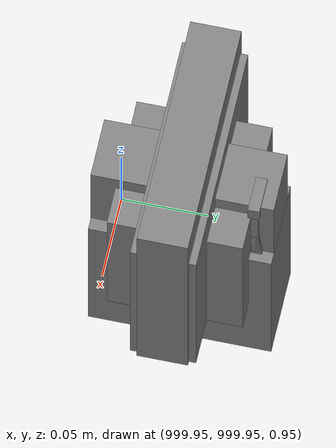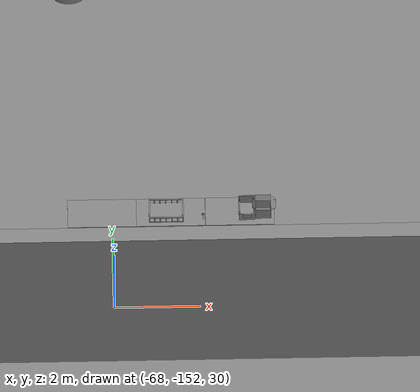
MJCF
<mujoco>
    <option gravity="0.000000000 0.000000000 -9.810000420" timestep="0.0049999999" integrator="implicitfast" density="1.225" viscosity="1.8000001e-05" noslip_iterations="10" iterations="100" sdf_iterations="50">
        <flag multiccd="disable"/>
    </option>
    <size memory="1000M"/>
    <compiler coordinate="local"/>
    <worldbody>
        <light cutoff="30" pos="0 1 1" dir="0 -1 -2"/>
        <light cutoff="30" pos="0 -1 1" dir="0 1 -2"/>
        <body pos="1000.000000000 1000.000000000 1.000000000" euler="0.000000000 0.000000000 180.000000000" name="openloong_gripper_2f85_fix_base_usda_battery_01">
            <geom contype="1" conaffinity="1" density="1000" type="box" material="" rgba="0.500000000 0.500000000 0.500000000 1.000000000" solimp="0.899999976 0.949999988 0.001000000" friction="1.000000000 0.005000000 0.000100000" solref="0.020000000 1.000000000" margin="0" condim="3" group="0" pos="-0.011123657 -0.041940309 0.101691343" quat="1.000000000 0.000000000 0.000000000 0.000000000" size="0.010800000 0.003375000 0.004725000" name="openloong_gripper_2f85_fix_base_usda_geom_5541FAD3_A0A6_4B7F_893C_FC5AA17A68BF"/>
            <geom contype="1" conaffinity="1" density="1000" type="box" material="" rgba="0.500000000 0.500000000 0.500000000 1.000000000" solimp="0.899999976 0.949999988 0.001000000" friction="1.000000000 0.005000000 0.000100000" solref="0.020000000 1.000000000" margin="0" condim="3" group="0" pos="-0.010876465 -0.044247437 0.047066893" quat="0.998702705 -0.050920475 0.000000000 0.000000000" size="0.009450001 0.002700000 0.024975000" name="openloong_gripper_2f85_fix_base_usda_geom_F9D04D68_3C9A_43C2_97DE_A756900556EE"/>
            <geom contype="1" conaffinity="1" density="1000" type="box" material="" rgba="0.500000000 0.500000000 0.500000000 1.000000000" solimp="0.899999976 0.949999988 0.001000000" friction="1.000000000 0.005000000 0.000100000" solref="0.020000000 1.000000000" margin="0" condim="3" group="0" pos="-0.001235962 -0.000659180 0.047381196" quat="1.000000000 0.000000000 0.000000000 0.000000000" size="0.039420001 0.039150000 0.047250003" name="openloong_gripper_2f85_fix_base_usda_geom_51BBA66F_5A15_4698_BD31_CACF67B96926"/>
            <geom contype="1" conaffinity="1" density="1000" type="box" material="" rgba="0.500000000 0.500000000 0.500000000 1.000000000" solimp="0.899999976 0.949999988 0.001000000" friction="1.000000000 0.005000000 0.000100000" solref="0.020000000 1.000000000" margin="0" condim="3" group="0" pos="-0.010876465 -0.039138794 0.009851727" quat="1.000000000 0.000000000 0.000000000 0.000000000" size="0.009450001 0.010800000 0.013500000" name="openloong_gripper_2f85_fix_base_usda_geom_3D07A4C8_CD27_42ED_9DC4_4D5C4513EE87"/>
            <geom contype="1" conaffinity="1" density="1000" type="box" material="" rgba="0.500000000 0.500000000 0.500000000 1.000000000" solimp="0.899999976 0.949999988 0.001000000" friction="1.000000000 0.005000000 0.000100000" solref="0.020000000 1.000000000" margin="0" condim="3" group="0" pos="-0.010876465 -0.041528322 0.071508206" quat="1.000000000 0.000000000 0.000000000 0.000000000" size="0.009450001 0.002700000 0.027000001" name="openloong_gripper_2f85_fix_base_usda_geom_4B9178BB_EC63_4CEC_9C2D_3E04820E38E1"/>
            <freejoint name="openloong_gripper_2f85_fix_base_usda_battery_01_joint"/>
            <site size="0.005000000 0.005000000 0.005000000" rgba="0.500000000 0.500000000 0.500000000 1.000000000" pos="0.000000000 0.000000000 0.000000000" quat="0.999961913 0.008726500 0.000000000 0.000000000" group="0" type="sphere" name="openloong_gripper_2f85_fix_base_usda_battery_01site"/>
        </body>
        <body pos="1000.000000000 1000.000000000 1.000000000" euler="0.000000000 0.000000000 180.000000000" name="openloong_gripper_2f85_fix_base_usda_wifi_box">
            <geom contype="1" conaffinity="1" density="1000" type="box" material="" rgba="0.500000000 0.500000000 0.500000000 1.000000000" solimp="0.899999976 0.949999988 0.001000000" friction="1.000000000 0.005000000 0.000100000" solref="0.020000000 1.000000000" margin="0" condim="3" group="0" pos="0.000000000 0.000000000 0.058978677" quat="0.000000000 0.000000047 0.000000000 1.000000000" size="0.068499997 0.018999999 0.059000000" name="openloong_gripper_2f85_fix_base_usda_geom_9DB1461D_779C_4E09_A75E_FACFB3D03746"/>
            <freejoint name="openloong_gripper_2f85_fix_base_usda_wifi_box_joint"/>
            <site size="0.005000000 0.005000000 0.005000000" rgba="0.500000000 0.500000000 0.500000000 1.000000000" pos="0.000000000 0.000000000 0.000000000" quat="0.999961913 0.008726500 0.000000000 0.000000000" group="0" type="sphere" name="openloong_gripper_2f85_fix_base_usda_wifi_boxsite"/>
        </body>
        <body pos="1000.000000000 1000.000000000 1.000000000" euler="0.000000000 0.000000000 180.000000000" name="openloong_gripper_2f85_fix_base_usda_cpu_fan">
            <geom contype="1" conaffinity="1" density="1000" type="box" material="" rgba="0.500000000 0.500000000 0.500000000 1.000000000" solimp="0.899999976 0.949999988 0.001000000" friction="1.000000000 0.005000000 0.000100000" solref="0.020000000 1.000000000" margin="0" condim="3" group="0" pos="0.000000000 0.000000000 0.070034981" quat="0.000000000 0.000000000 0.000000000 1.000000000" size="0.070700005 0.014699999 0.070700005" name="openloong_gripper_2f85_fix_base_usda_geom_1A41D756_01A4_4861_8EB2_B8255C0A081E"/>
            <freejoint name="openloong_gripper_2f85_fix_base_usda_cpu_fan_joint"/>
            <site size="0.005000000 0.005000000 0.005000000" rgba="0.500000000 0.500000000 0.500000000 1.000000000" pos="0.000000000 0.000000000 0.000000000" quat="0.999961913 0.008726535 0.000000000 0.000000000" group="0" type="sphere" name="openloong_gripper_2f85_fix_base_usda_cpu_fancsite"/>
        </body>
        <body pos="-66.350883484 -149.156921387 31.167390823" euler="-82.256919861 77.681053162 -126.587661743" mocap="true" name="spotlight6_SpotLight"/>
        <body pos="1000.000000000 1000.000000000 1.000000000" euler="0.000011953 0.000005123 -179.999984741" name="openloong_gripper_2f85_fix_base_usda_intel_box">
            <geom contype="1" conaffinity="1" density="1000" type="box" material="" rgba="0.500000000 0.500000000 0.500000000 1.000000000" solimp="0.899999976 0.949999988 0.001000000" friction="1.000000000 0.005000000 0.000100000" solref="0.020000000 1.000000000" margin="0" condim="3" group="0" pos="0.000000000 -0.000067139 0.000082284" quat="0.707106709 0.000000225 0.000000253 0.707106650" size="0.052800003 0.025300000 0.052800003" name="openloong_gripper_2f85_fix_base_usda_geom_53EB4B6A_65C6_4498_BAEC_828C5240226B"/>
            <freejoint name="openloong_gripper_2f85_fix_base_usda_intel_box_joint"/>
            <site size="0.005000000 0.005000000 0.005000000" rgba="0.500000000 0.500000000 0.500000000 1.000000000" pos="0.000000000 0.000000000 0.000000000" quat="0.999961913 0.008726500 0.000000000 0.000000000" group="0" type="sphere" name="openloong_gripper_2f85_fix_base_usda_intel_boxsite"/>
        </body>
        <body pos="-66.207199097 -149.536529541 31.162195206" euler="-33.667755127 -4.240795135 113.501518250" mocap="true" name="spotlight5_SpotLight"/>
        <body pos="1000.000000000 999.999938965 1.000000000" euler="0.000000000 0.000000000 180.000000000" name="openloong_gripper_2f85_fix_base_usda_intelcore_i5">
            <geom contype="1" conaffinity="1" density="1000" type="box" material="" rgba="0.500000000 0.500000000 0.500000000 1.000000000" solimp="0.899999976 0.949999988 0.001000000" friction="1.000000000 0.005000000 0.000100000" solref="0.020000000 1.000000000" margin="0" condim="3" group="0" pos="0.000000000 0.000000000 0.051722717" quat="0.707106709 0.000000000 0.000000000 -0.707106769" size="0.052800000 0.018080002 0.052800000" name="openloong_gripper_2f85_fix_base_usda_geom_B916976F_4ABB_46E4_964E_6D927303FF69"/>
            <freejoint name="openloong_gripper_2f85_fix_base_usda_intelcore_i5_joint"/>
            <site size="0.005000000 0.005000000 0.005000000" rgba="0.500000000 0.500000000 0.500000000 1.000000000" pos="0.000000000 0.000000000 0.000000000" quat="0.999961913 0.008726534 0.000000000 0.000000000" group="0" type="sphere" name="openloong_gripper_2f85_fix_base_usda_intelcore_i5site"/>
        </body>
        <body pos="-65.994796753 -149.405471802 31.169294357" euler="-141.169677734 -54.483589172 40.411651611" mocap="true" name="spotlight4_SpotLight"/>
        <body pos="-64.866622925 -149.383972168 30.183746338" euler="89.999984741 89.999946594 0.000000000" name="openloong_gripper_2f85_fix_base_usda_bluebox_01">
            <geom contype="1" conaffinity="1" density="1000" type="box" material="" rgba="0.500000000 0.500000000 0.500000000 1.000000000" solimp="0.899999976 0.949999988 0.001000000" friction="1.000000000 0.005000000 0.000100000" solref="0.020000000 1.000000000" margin="0" condim="3" group="0" pos="0.276580811 0.187225342 0.000068665" quat="0.707106948 0.000077471 0.707106352 0.000077486" size="0.100000001 0.057999998 0.010000000" name="openloong_gripper_2f85_fix_base_usda_geom_71354975_F7C8_4FEE_9C11_08B52D43953D"/>
            <geom contype="1" conaffinity="1" density="1000" type="box" material="" rgba="0.500000000 0.500000000 0.500000000 1.000000000" solimp="0.899999976 0.949999988 0.001000000" friction="1.000000000 0.005000000 0.000100000" solref="0.020000000 1.000000000" margin="0" condim="3" group="0" pos="0.000000000 0.002883911 0.000000000" quat="0.999999881 0.000000000 0.000000000 0.000000000" size="0.254000008 0.003000000 0.172000006" name="openloong_gripper_2f85_fix_base_usda_geom_19EA5BAD_A32E_4301_813A_5E1020B66620"/>
            <geom contype="1" conaffinity="1" density="1000" type="box" material="" rgba="0.500000000 0.500000000 0.500000000 1.000000000" solimp="0.899999976 0.949999988 0.001000000" friction="1.000000000 0.005000000 0.000100000" solref="0.020000000 1.000000000" margin="0" condim="3" group="0" pos="0.000000000 0.124874115 0.173484802" quat="0.999796331 0.020176515 -0.000000015 0.000000030" size="0.259999990 0.119999997 0.007000000" name="openloong_gripper_2f85_fix_base_usda_geom_BA5551FD_828C_49B1_A0DD_75430C83C980"/>
            <geom contype="1" conaffinity="1" density="1000" type="box" material="" rgba="0.500000000 0.500000000 0.500000000 1.000000000" solimp="0.899999976 0.949999988 0.001000000" friction="1.000000000 0.005000000 0.000100000" solref="0.020000000 1.000000000" margin="0" condim="3" group="0" pos="0.000000000 0.124874115 -0.173469543" quat="0.999796331 -0.020176545 -0.000000015 0.000000000" size="0.259999990 0.119999997 0.007000000" name="openloong_gripper_2f85_fix_base_usda_geom_7FC81764_9FD4_4BC9_94EF_01B66CBE0D04"/>
            <geom contype="1" conaffinity="1" density="1000" type="box" material="" rgba="0.500000000 0.500000000 0.500000000 1.000000000" solimp="0.899999976 0.949999988 0.001000000" friction="1.000000000 0.005000000 0.000100000" solref="0.020000000 1.000000000" margin="0" condim="3" group="0" pos="0.000000000 0.214008331 0.188980103" quat="0.999912977 0.013176724 0.000000015 0.000000000" size="0.259999990 0.029999999 0.012500000" name="openloong_gripper_2f85_fix_base_usda_geom_7FFBCB34_6293_4FD4_9FA0_1DB09E05B84A"/>
            <geom contype="1" conaffinity="1" density="1000" type="box" material="" rgba="0.500000000 0.500000000 0.500000000 1.000000000" solimp="0.899999976 0.949999988 0.001000000" friction="1.000000000 0.005000000 0.000100000" solref="0.020000000 1.000000000" margin="0" condim="3" group="0" pos="-0.258361816 0.125289917 0.001876831" quat="0.702796936 -0.020792112 0.710783124 0.020769298" size="0.189999998 0.119999997 0.009000000" name="openloong_gripper_2f85_fix_base_usda_geom_9F01E509_3385_4F16_A054_3C516A56F3B5"/>
            <geom contype="1" conaffinity="1" density="1000" type="box" material="" rgba="0.500000000 0.500000000 0.500000000 1.000000000" solimp="0.899999976 0.949999988 0.001000000" friction="1.000000000 0.005000000 0.000100000" solref="0.020000000 1.000000000" margin="0" condim="3" group="0" pos="0.000000000 0.214008331 -0.188980103" quat="0.999912977 -0.013176769 0.000000030 0.000000015" size="0.259999990 0.029999999 0.012500000" name="openloong_gripper_2f85_fix_base_usda_geom_5A79D8AA_F90B_44C3_AEA2_03E2EF327FF9"/>
            <geom contype="1" conaffinity="1" density="1000" type="box" material="" rgba="0.500000000 0.500000000 0.500000000 1.000000000" solimp="0.899999976 0.949999988 0.001000000" friction="1.000000000 0.005000000 0.000100000" solref="0.020000000 1.000000000" margin="0" condim="3" group="0" pos="-0.276611328 0.187225342 0.000068665" quat="0.707106650 0.000077441 0.707106709 0.000077456" size="0.100000001 0.057999998 0.010000000" name="openloong_gripper_2f85_fix_base_usda_geom_34DCC427_35D3_45A4_B73F_73747823850E"/>
            <geom contype="1" conaffinity="1" density="1000" type="box" material="" rgba="0.500000000 0.500000000 0.500000000 1.000000000" solimp="0.899999976 0.949999988 0.001000000" friction="1.000000000 0.005000000 0.000100000" solref="0.020000000 1.000000000" margin="0" condim="3" group="0" pos="0.258331299 0.125289917 0.001876831" quat="0.702851415 0.018856421 0.710823774 -0.019329369" size="0.189999998 0.119999997 0.009000000" name="openloong_gripper_2f85_fix_base_usda_geom_61B78F5E_197A_45AF_89EB_30700D47FC52"/>
            <freejoint name="openloong_gripper_2f85_fix_base_usda_bluebox_01_joint"/>
            <site size="0.005000000 0.005000000 0.005000000" rgba="0.500000000 0.500000000 0.500000000 1.000000000" pos="0.000000000 0.000000000 0.000000000" quat="0.999961913 0.008726534 0.000000000 0.000000000" group="0" type="sphere" name="openloong_gripper_2f85_fix_base_usda_bluebox_01site"/>
        </body>
        <body pos="-64.496299744 -149.491867065 30.235729218" euler="0.000000000 0.000000000 89.999946594" name="openloong_gripper_2f85_fix_base_usda_cardboardbox_01">
            <geom contype="1" conaffinity="1" density="1000" type="box" material="" rgba="0.500000000 0.500000000 0.500000000 1.000000000" solimp="0.899999976 0.949999988 0.001000000" friction="1.000000000 0.005000000 0.000100000" solref="0.020000000 1.000000000" margin="0" condim="3" group="0" pos="-0.003166199 -0.004086494 0.005052090" quat="1.000000000 0.000000000 0.000000000 0.000000000" size="0.142499998 0.177500010 0.005000000" name="openloong_gripper_2f85_fix_base_usda_geom_E6E5C942_E2B2_4B3C_9709_0CB52A1AA6A8"/>
            <geom contype="1" conaffinity="1" density="1000" type="box" material="" rgba="0.500000000 0.500000000 0.500000000 1.000000000" solimp="0.899999976 0.949999988 0.001000000" friction="1.000000000 0.005000000 0.000100000" solref="0.020000000 1.000000000" margin="0" condim="3" group="0" pos="-0.003166199 0.170316696 0.150570869" quat="1.000000000 0.000000000 0.000000000 0.000000000" size="0.142499998 0.005000000 0.149999991" name="openloong_gripper_2f85_fix_base_usda_geom_D074AB4C_E1CB_49E6_9EFF_E607622CA5E4"/>
            <geom contype="1" conaffinity="1" density="1000" type="box" material="" rgba="0.500000000 0.500000000 0.500000000 1.000000000" solimp="0.899999976 0.949999988 0.001000000" friction="1.000000000 0.005000000 0.000100000" solref="0.020000000 1.000000000" margin="0" condim="3" group="0" pos="-0.147399902 -0.005307198 0.150570869" quat="1.000000000 0.000000000 0.000000000 0.000000000" size="0.005000000 0.177500010 0.149999991" name="openloong_gripper_2f85_fix_base_usda_geom_52232EB3_0E13_463F_83A4_42292CC36F2C"/>
            <geom contype="1" conaffinity="1" density="1000" type="box" material="" rgba="0.500000000 0.500000000 0.500000000 1.000000000" solimp="0.899999976 0.949999988 0.001000000" friction="1.000000000 0.005000000 0.000100000" solref="0.020000000 1.000000000" margin="0" condim="3" group="0" pos="0.140275955 -0.005307198 0.150570869" quat="1.000000000 0.000000000 0.000000000 0.000000000" size="0.005000000 0.177500010 0.149999991" name="openloong_gripper_2f85_fix_base_usda_geom_0655B411_48C2_4A21_9F2E_D84FAB24DDC3"/>
            <geom contype="1" conaffinity="1" density="1000" type="box" material="" rgba="0.500000000 0.500000000 0.500000000 1.000000000" solimp="0.899999976 0.949999988 0.001000000" friction="1.000000000 0.005000000 0.000100000" solref="0.020000000 1.000000000" margin="0" condim="3" group="0" pos="-0.003166199 -0.181550980 0.150570869" quat="1.000000000 0.000000000 0.000000000 0.000000000" size="0.142499998 0.005000000 0.149999991" name="openloong_gripper_2f85_fix_base_usda_geom_6365FBFF_184A_49DF_A2FE_AAF7624C78BF"/>
            <freejoint name="openloong_gripper_2f85_fix_base_usda_cardboardbox_01_joint"/>
            <site size="0.005000000 0.005000000 0.005000000" rgba="0.500000000 0.500000000 0.500000000 1.000000000" pos="0.000000000 0.000000000 0.000000000" quat="0.999961913 0.008726535 0.000000000 0.000000000" group="0" type="sphere" name="openloong_gripper_2f85_fix_base_usda_site_6442569C_1635_4298_BF2D_749CA34C4EFD"/>
            <body pos="0.139160156 -0.004048347 0.301930904" euler="-179.999954224 49.383502960 179.999954224" name="openloong_gripper_2f85_fix_base_usda_A1_006">
                <geom contype="1" conaffinity="1" density="1000" type="box" material="" rgba="0.500000000 0.500000000 0.500000000 1.000000000" solimp="0.899999976 0.949999988 0.001000000" friction="1.000000000 0.005000000 0.000100000" solref="0.020000000 1.000000000" margin="0" condim="3" group="0" pos="-0.071587563 0.000009537 0.001745224" quat="0.999999881 0.000000000 0.000000000 0.000000000" size="0.071249999 0.179999992 0.002500000" name="openloong_gripper_2f85_fix_base_usda_geom_6F2BAAB8_C38F_4654_9167_97AB8B7A539C"/>
                <joint armature="0" stiffness="0.07" damping="0.0099999998" axis="0.000000 1.000000 0.000000" type="hinge" name="openloong_gripper_2f85_fix_base_usda_A1_006"/>
            </body>
            <body pos="-0.145902634 -0.004086494 0.301938057" euler="-180.000000000 -60.000011444 -180.000000000" name="openloong_gripper_2f85_fix_base_usda_A2_006">
                <geom contype="1" conaffinity="1" density="1000" type="box" material="" rgba="0.500000000 0.500000000 0.500000000 1.000000000" solimp="0.899999976 0.949999988 0.001000000" friction="1.000000000 0.005000000 0.000100000" solref="0.020000000 1.000000000" margin="0" condim="3" group="0" pos="0.071268082 0.000009537 0.002717972" quat="0.000002921 0.000000000 -0.000000030 0.999999881" size="0.071249999 0.179999992 0.002500000" name="openloong_gripper_2f85_fix_base_usda_geom_52E71D37_9873_4CED_AD70_66E32278F8B5"/>
                <joint armature="0" stiffness="0.07" damping="0.0099999998" axis="0.000000 1.000000 0.000000" type="hinge" name="openloong_gripper_2f85_fix_base_usda_A2_006"/>
            </body>
            <body pos="-0.003385544 0.175991058 0.301930904" euler="-125.858116150 -0.000004561 0.000002331" name="openloong_gripper_2f85_fix_base_usda_B2_006">
                <geom contype="1" conaffinity="1" density="1000" type="box" material="" rgba="0.500000000 0.500000000 0.500000000 1.000000000" solimp="0.899999976 0.949999988 0.001000000" friction="1.000000000 0.005000000 0.000100000" solref="0.020000000 1.000000000" margin="0" condim="3" group="0" pos="0.000009537 -0.070939064 -0.002470016" quat="0.999614120 0.027776197 -0.000000015 0.000000030" size="0.137500003 0.064999998 0.005000000" name="openloong_gripper_2f85_fix_base_usda_geom_F74B91E2_3951_4B64_BCC0_893100C5724C"/>
                <joint armature="0" stiffness="0.07" damping="0.0099999998" axis="1.000000 0.000000 0.000000" type="hinge" name="openloong_gripper_2f85_fix_base_usda_B2_006"/>
            </body>
            <body pos="-0.003385544 -0.184140205 0.301938057" euler="147.805557251 0.000000000 0.000000000" name="openloong_gripper_2f85_fix_base_usda_B1_006">
                <geom contype="1" conaffinity="1" density="1000" type="box" material="" rgba="0.500000000 0.500000000 0.500000000 1.000000000" solimp="0.899999976 0.949999988 0.001000000" friction="1.000000000 0.005000000 0.000100000" solref="0.020000000 1.000000000" margin="0" condim="3" group="0" pos="-0.000028610 0.070202351 -0.002703667" quat="0.999614179 -0.027776167 0.000000000 0.000000000" size="0.137500003 0.064999998 0.005000000" name="openloong_gripper_2f85_fix_base_usda_geom_823195DD_9F8B_4EEA_81D1_DE422BA20004"/>
                <joint armature="0" stiffness="0.07" damping="0.0099999998" axis="1.000000 0.000000 0.000000" type="hinge" name="openloong_gripper_2f85_fix_base_usda_B1_006"/>
            </body>
        </body>
        <body pos="-65.882858276 -149.481979370 30.229999542" euler="-64.487716675 0.000000000 0.000000000" name="openloong_gripper_2f85_fix_base_usda_Barcode">
            <geom contype="1" conaffinity="1" density="1000" type="box" material="" rgba="0.500000000 0.500000000 0.500000000 1.000000000" solimp="0.899999976 0.949999988 0.001000000" friction="1.000000000 0.005000000 0.000100000" solref="0.020000000 1.000000000" margin="0" condim="3" group="0" pos="0.000000000 0.013038635 0.001419067" quat="0.000000000 0.000000000 0.000000000 1.000000119" size="0.034000002 0.010000000 0.017999999" name="openloong_gripper_2f85_fix_base_usda_geom_4C53E1F8_DF06_4ABA_A5EC_DE6677881C97"/>
            <geom contype="1" conaffinity="1" density="1000" type="box" material="" rgba="0.500000000 0.500000000 0.500000000 1.000000000" solimp="0.899999976 0.949999988 0.001000000" friction="1.000000000 0.005000000 0.000100000" solref="0.020000000 1.000000000" margin="0" condim="3" group="0" pos="0.000000000 -0.035301208 -0.007095337" quat="0.000000000 0.000000000 -0.043619365 0.999048233" size="0.028999999 0.010000000 0.020000000" name="openloong_gripper_2f85_fix_base_usda_geom_F4F90DAF_C849_4F86_808A_AD913F9423CA"/>
            <geom contype="1" conaffinity="1" density="1000" type="box" material="" rgba="0.500000000 0.500000000 0.500000000 1.000000000" solimp="0.899999976 0.949999988 0.001000000" friction="1.000000000 0.005000000 0.000100000" solref="0.020000000 1.000000000" margin="0" condim="3" group="0" pos="0.000000000 -0.043411255 -0.011749268" quat="0.922262907 0.386563420 0.000000000 0.000000000" size="0.026000001 0.010000000 0.020000000" name="openloong_gripper_2f85_fix_base_usda_geom_6E9CCDB3_B3D3_4C32_9BC7_8243A3D37FD8"/>
            <geom contype="1" conaffinity="1" density="1000" type="box" material="" rgba="0.500000000 0.500000000 0.500000000 1.000000000" solimp="0.899999976 0.949999988 0.001000000" friction="1.000000000 0.005000000 0.000100000" solref="0.020000000 1.000000000" margin="0" condim="3" group="0" pos="0.000000000 -0.016967773 -0.031860352" quat="0.000000000 0.000000000 0.000000000 1.000000119" size="0.008000000 0.010000000 0.013000000" name="openloong_gripper_2f85_fix_base_usda_geom_FBF20260_7461_4557_B72E_7AE7BC2D72FF"/>
            <geom contype="1" conaffinity="1" density="1000" type="box" material="" rgba="0.500000000 0.500000000 0.500000000 1.000000000" solimp="0.899999976 0.949999988 0.001000000" friction="1.000000000 0.005000000 0.000100000" solref="0.020000000 1.000000000" margin="0" condim="3" group="0" pos="0.000000000 -0.001869202 0.000312805" quat="0.953716993 0.300705761 0.000000000 0.000000000" size="0.032000002 0.010000000 0.018999999" name="openloong_gripper_2f85_fix_base_usda_geom_281CCC20_8622_4C82_BB91_26A9CDEAD6C3"/>
            <geom contype="1" conaffinity="1" density="1000" type="box" material="" rgba="0.500000000 0.500000000 0.500000000 1.000000000" solimp="0.899999976 0.949999988 0.001000000" friction="1.000000000 0.005000000 0.000100000" solref="0.020000000 1.000000000" margin="0" condim="3" group="0" pos="0.000000000 -0.019531250 -0.003173828" quat="0.953716993 0.300705761 0.000000000 0.000000000" size="0.030999999 0.010000000 0.020000000" name="openloong_gripper_2f85_fix_base_usda_geom_2BC137EC_B61E_4A26_8F50_0D6039F0409A"/>
            <geom contype="1" conaffinity="1" density="1000" type="box" material="" rgba="0.500000000 0.500000000 0.500000000 1.000000000" solimp="0.899999976 0.949999988 0.001000000" friction="1.000000000 0.005000000 0.000100000" solref="0.020000000 1.000000000" margin="0" condim="3" group="0" pos="0.000000000 -0.035301208 -0.007095337" quat="0.953716993 0.300705761 0.000000000 0.000000000" size="0.028999999 0.010000000 0.020000000" name="openloong_gripper_2f85_fix_base_usda_geom_F5BEF7DB_6CBA_4B2F_8E7A_17D758B5D38E"/>
            <geom contype="1" conaffinity="1" density="1000" type="box" material="" rgba="0.500000000 0.500000000 0.500000000 1.000000000" solimp="0.899999976 0.949999988 0.001000000" friction="1.000000000 0.005000000 0.000100000" solref="0.020000000 1.000000000" margin="0" condim="3" group="0" pos="0.000000000 -0.042617798 -0.071121216" quat="0.000000000 0.000000000 0.000000000 1.000000119" size="0.013000000 0.021000000 0.059999999" name="openloong_gripper_2f85_fix_base_usda_geom_1085D449_8D8E_42EE_81D7_09F55BB6300F"/>
            <freejoint name="openloong_gripper_2f85_fix_base_usda_Barcode_joint"/>
            <site size="0.005000000 0.005000000 0.005000000" rgba="0.500000000 0.500000000 0.500000000 1.000000000" pos="0.000000000 0.000000000 0.000000000" quat="1.000000000 0.000000000 0.000000000 0.000000000" group="0" type="sphere" name="openloong_gripper_2f85_fix_base_usda_Barcode_site"/>
        </body>
        <body pos="-66.745018005 -149.392349243 30.184000015" euler="0.000000000 0.000000000 89.999946594" name="[22330088738536]_Basket_01">
            <geom contype="1" conaffinity="1" density="1000" type="box" material="" rgba="0.500000000 0.500000000 0.500000000 1.000000000" solimp="0.899999976 0.949999988 0.001000000" friction="1.000000000 0.005000000 0.000100000" solref="0.020000000 1.000000000" margin="0" condim="3" group="0" pos="-0.052425385 0.389207840 0.089787483" quat="0.707107008 0.000000000 0.000000000 0.707106411" size="0.014249999 0.014249999 0.059999999" name="[22330088738536]_geom_C7AAA6DD_5D25_4A23_BBC0_B996AF10FC5E"/>
            <geom contype="1" conaffinity="1" density="1000" type="box" material="" rgba="0.500000000 0.500000000 0.500000000 1.000000000" solimp="0.899999976 0.949999988 0.001000000" friction="1.000000000 0.005000000 0.000100000" solref="0.020000000 1.000000000" margin="0" condim="3" group="0" pos="0.264015198 -0.133043289 0.089787483" quat="0.707107008 0.000000000 0.000000000 0.707106411" size="0.014249999 0.014249999 0.059999999" name="[22330088738536]_geom_77AB3A83_F088_4D17_A314_6AD9405F6F6F"/>
            <geom contype="1" conaffinity="1" density="1000" type="box" material="" rgba="0.500000000 0.500000000 0.500000000 1.000000000" solimp="0.899999976 0.949999988 0.001000000" friction="1.000000000 0.005000000 0.000100000" solref="0.020000000 1.000000000" margin="0" condim="3" group="0" pos="-0.264015198 -0.265548706 0.089793205" quat="0.707107008 0.000000000 0.000000000 0.707106411" size="0.014249999 0.014249999 0.059999999" name="[22330088738536]_geom_B6393529_2B17_4E1A_A863_00D041F94AFC"/>
            <geom contype="1" conaffinity="1" density="1000" type="box" material="" rgba="0.500000000 0.500000000 0.500000000 1.000000000" solimp="0.899999976 0.949999988 0.001000000" friction="1.000000000 0.005000000 0.000100000" solref="0.020000000 1.000000000" margin="0" condim="3" group="0" pos="-0.160263062 -0.389322281 0.089793205" quat="0.707107008 0.000000000 0.000000000 0.707106411" size="0.014249999 0.014249999 0.059999999" name="[22330088738536]_geom_62B3BBC4_7EFE_42CC_B659_B7BE987E82A3"/>
            <geom contype="1" conaffinity="1" density="1000" type="box" material="" rgba="0.500000000 0.500000000 0.500000000 1.000000000" solimp="0.899999976 0.949999988 0.001000000" friction="1.000000000 0.005000000 0.000100000" solref="0.020000000 1.000000000" margin="0" condim="3" group="0" pos="0.162265778 -0.389322281 0.089787483" quat="0.707107008 0.000000000 0.000000000 0.707106411" size="0.014249999 0.014249999 0.059999999" name="[22330088738536]_geom_4AC25CED_7E36_4A8A_9BD2_5D60F13F7ED5"/>
            <geom contype="1" conaffinity="1" density="1000" type="box" material="" rgba="0.500000000 0.500000000 0.500000000 1.000000000" solimp="0.899999976 0.949999988 0.001000000" friction="1.000000000 0.005000000 0.000100000" solref="0.020000000 1.000000000" margin="0" condim="3" group="0" pos="0.264015198 0.389207840 0.089787483" quat="0.707107008 0.000000000 0.000000000 0.707106411" size="0.014249999 0.014249999 0.059999999" name="[22330088738536]_geom_CADA6332_898A_48E7_9F1B_C8DF8D1F80E7"/>
            <geom contype="1" conaffinity="1" density="1000" type="box" material="" rgba="0.500000000 0.500000000 0.500000000 1.000000000" solimp="0.899999976 0.949999988 0.001000000" friction="1.000000000 0.005000000 0.000100000" solref="0.020000000 1.000000000" margin="0" condim="3" group="0" pos="-0.264015198 -0.133043289 0.089793205" quat="0.707107008 0.000000000 0.000000000 0.707106411" size="0.014249999 0.014249999 0.059999999" name="[22330088738536]_geom_00EC265C_526C_4230_9872_BC014F358CCB"/>
            <geom contype="1" conaffinity="1" density="1000" type="box" material="" rgba="0.500000000 0.500000000 0.500000000 1.000000000" solimp="0.899999976 0.949999988 0.001000000" friction="1.000000000 0.005000000 0.000100000" solref="0.020000000 1.000000000" margin="0" condim="3" group="0" pos="-0.264026642 0.269256592 0.089793205" quat="0.707107008 0.000000000 0.000000000 0.707106411" size="0.014249999 0.014249999 0.059999999" name="[22330088738536]_geom_5EE97EB0_BBD5_46E8_BB8A_40BDF9F01198"/>
            <geom contype="1" conaffinity="1" density="1000" type="box" material="" rgba="0.500000000 0.500000000 0.500000000 1.000000000" solimp="0.899999976 0.949999988 0.001000000" friction="1.000000000 0.005000000 0.000100000" solref="0.020000000 1.000000000" margin="0" condim="3" group="0" pos="0.054462433 0.389207840 0.089787483" quat="0.707107008 0.000000000 0.000000000 0.707106411" size="0.014249999 0.014249999 0.059999999" name="[22330088738536]_geom_B4820849_618B_4524_9124_07ACBB8574F6"/>
            <geom contype="1" conaffinity="1" density="1000" type="box" material="" rgba="0.500000000 0.500000000 0.500000000 1.000000000" solimp="0.899999976 0.949999988 0.001000000" friction="1.000000000 0.005000000 0.000100000" solref="0.020000000 1.000000000" margin="0" condim="3" group="0" pos="0.054462433 -0.389322281 0.089787483" quat="0.707107008 0.000000000 0.000000000 0.707106411" size="0.014249999 0.014249999 0.059999999" name="[22330088738536]_geom_3020F932_94AE_4829_8CDC_6CD2DB4E0130"/>
            <geom contype="1" conaffinity="1" density="1000" type="box" material="" rgba="0.500000000 0.500000000 0.500000000 1.000000000" solimp="0.899999976 0.949999988 0.001000000" friction="1.000000000 0.005000000 0.000100000" solref="0.020000000 1.000000000" margin="0" condim="3" group="0" pos="0.264015198 0.269256592 0.089793205" quat="0.707107008 0.000000000 0.000000000 0.707106411" size="0.014249999 0.014249999 0.059999999" name="[22330088738536]_geom_A255A760_A5F0_4057_A5E3_33A0F85D6D6A"/>
            <geom contype="1" conaffinity="1" density="1000" type="box" material="" rgba="0.500000000 0.500000000 0.500000000 1.000000000" solimp="0.899999976 0.949999988 0.001000000" friction="1.000000000 0.005000000 0.000100000" solref="0.020000000 1.000000000" margin="0" condim="3" group="0" pos="0.264015198 -0.389322281 0.089787483" quat="0.707107008 0.000000000 0.000000000 0.707106411" size="0.014249999 0.014249999 0.059999999" name="[22330088738536]_geom_1331EE51_F9EC_47DA_B53A_BC4804572B96"/>
            <geom contype="1" conaffinity="1" density="1000" type="box" material="" rgba="0.500000000 0.500000000 0.500000000 1.000000000" solimp="0.899999976 0.949999988 0.001000000" friction="1.000000000 0.005000000 0.000100000" solref="0.020000000 1.000000000" margin="0" condim="3" group="0" pos="0.000000000 0.000000000 0.015998840" quat="0.707107008 0.000000000 0.000000000 0.707106411" size="0.403499991 0.279000014 0.015750000" name="[22330088738536]_geom_DCEDFC31_AFD8_4A1E_B2F7_718E27ACF632"/>
            <geom contype="1" conaffinity="1" density="1000" type="box" material="" rgba="0.500000000 0.500000000 0.500000000 1.000000000" solimp="0.899999976 0.949999988 0.001000000" friction="1.000000000 0.005000000 0.000100000" solref="0.020000000 1.000000000" margin="0" condim="3" group="0" pos="0.000000000 -0.389476776 0.163619041" quat="0.707107008 0.000000000 0.000000000 0.707106411" size="0.015000000 0.277500004 0.015750000" name="[22330088738536]_geom_81D75298_2213_4AA8_B829_EE56F7862C02"/>
            <geom contype="1" conaffinity="1" density="1000" type="box" material="" rgba="0.500000000 0.500000000 0.500000000 1.000000000" solimp="0.899999976 0.949999988 0.001000000" friction="1.000000000 0.005000000 0.000100000" solref="0.020000000 1.000000000" margin="0" condim="3" group="0" pos="0.162265778 0.389207840 0.089787483" quat="0.707107008 0.000000000 0.000000000 0.707106411" size="0.014249999 0.014249999 0.059999999" name="[22330088738536]_geom_08B7F8FD_8A14_4197_A0E5_5D3F90782AFA"/>
            <geom contype="1" conaffinity="1" density="1000" type="box" material="" rgba="0.500000000 0.500000000 0.500000000 1.000000000" solimp="0.899999976 0.949999988 0.001000000" friction="1.000000000 0.005000000 0.000100000" solref="0.020000000 1.000000000" margin="0" condim="3" group="0" pos="0.000000000 0.389471054 0.163619041" quat="0.707107008 0.000000000 0.000000000 0.707106411" size="0.015000000 0.277500004 0.015750000" name="[22330088738536]_geom_8ED3D8B8_477F_4495_878D_6DE81C09F3ED"/>
            <geom contype="1" conaffinity="1" density="1000" type="box" material="" rgba="0.500000000 0.500000000 0.500000000 1.000000000" solimp="0.899999976 0.949999988 0.001000000" friction="1.000000000 0.005000000 0.000100000" solref="0.020000000 1.000000000" margin="0" condim="3" group="0" pos="-0.263511658 0.000000000 0.163619041" quat="0.707107008 0.000000000 0.000000000 0.707106411" size="0.403499991 0.015000000 0.015750000" name="[22330088738536]_geom_D9F2A965_9E72_482E_9665_9E0B69E713E4"/>
            <geom contype="1" conaffinity="1" density="1000" type="box" material="" rgba="0.500000000 0.500000000 0.500000000 1.000000000" solimp="0.899999976 0.949999988 0.001000000" friction="1.000000000 0.005000000 0.000100000" solref="0.020000000 1.000000000" margin="0" condim="3" group="0" pos="-0.264015198 0.141334534 0.089793205" quat="0.707107008 0.000000000 0.000000000 0.707106411" size="0.014249999 0.014249999 0.059999999" name="[22330088738536]_geom_13870618_A1E9_4284_81E0_71477B1CB5A5"/>
            <geom contype="1" conaffinity="1" density="1000" type="box" material="" rgba="0.500000000 0.500000000 0.500000000 1.000000000" solimp="0.899999976 0.949999988 0.001000000" friction="1.000000000 0.005000000 0.000100000" solref="0.020000000 1.000000000" margin="0" condim="3" group="0" pos="0.264015198 -0.265548706 0.089787483" quat="0.707107008 0.000000000 0.000000000 0.707106411" size="0.014249999 0.014249999 0.059999999" name="[22330088738536]_geom_9AB2EC82_D076_435F_8149_B7535303ACED"/>
            <geom contype="1" conaffinity="1" density="1000" type="box" material="" rgba="0.500000000 0.500000000 0.500000000 1.000000000" solimp="0.899999976 0.949999988 0.001000000" friction="1.000000000 0.005000000 0.000100000" solref="0.020000000 1.000000000" margin="0" condim="3" group="0" pos="-0.160263062 0.389207840 0.089787483" quat="0.707107008 0.000000000 0.000000000 0.707106411" size="0.014249999 0.014249999 0.059999999" name="[22330088738536]_geom_34EC8B05_1A98_4F30_8C98_369E501704B3"/>
            <geom contype="1" conaffinity="1" density="1000" type="box" material="" rgba="0.500000000 0.500000000 0.500000000 1.000000000" solimp="0.899999976 0.949999988 0.001000000" friction="1.000000000 0.005000000 0.000100000" solref="0.020000000 1.000000000" margin="0" condim="3" group="0" pos="-0.052425385 -0.389322281 0.089787483" quat="0.707107008 0.000000000 0.000000000 0.707106411" size="0.014249999 0.014249999 0.059999999" name="[22330088738536]_geom_A7FBD50D_6CFD_4095_91C1_3A03D9AE5F5D"/>
            <geom contype="1" conaffinity="1" density="1000" type="box" material="" rgba="0.500000000 0.500000000 0.500000000 1.000000000" solimp="0.899999976 0.949999988 0.001000000" friction="1.000000000 0.005000000 0.000100000" solref="0.020000000 1.000000000" margin="0" condim="3" group="0" pos="-0.264026642 -0.389322281 0.089793205" quat="0.707107008 0.000000000 0.000000000 0.707106411" size="0.014249999 0.014249999 0.059999999" name="[22330088738536]_geom_1691BF90_DEC0_4A24_BEE4_19B8908A608C"/>
            <geom contype="1" conaffinity="1" density="1000" type="box" material="" rgba="0.500000000 0.500000000 0.500000000 1.000000000" solimp="0.899999976 0.949999988 0.001000000" friction="1.000000000 0.005000000 0.000100000" solref="0.020000000 1.000000000" margin="0" condim="3" group="0" pos="0.264015198 0.141334534 0.089787483" quat="0.707107008 0.000000000 0.000000000 0.707106411" size="0.014249999 0.014249999 0.059999999" name="[22330088738536]_geom_6468A45A_2CC2_4588_A0EB_52B7ED02191D"/>
            <geom contype="1" conaffinity="1" density="1000" type="box" material="" rgba="0.500000000 0.500000000 0.500000000 1.000000000" solimp="0.899999976 0.949999988 0.001000000" friction="1.000000000 0.005000000 0.000100000" solref="0.020000000 1.000000000" margin="0" condim="3" group="0" pos="-0.264015198 0.389207840 0.089793205" quat="0.707107008 0.000000000 0.000000000 0.707106411" size="0.014249999 0.014249999 0.059999999" name="[22330088738536]_geom_48FCA26D_F9DC_41ED_829E_CB70147654E1"/>
            <geom contype="1" conaffinity="1" density="1000" type="box" material="" rgba="0.500000000 0.500000000 0.500000000 1.000000000" solimp="0.899999976 0.949999988 0.001000000" friction="1.000000000 0.005000000 0.000100000" solref="0.020000000 1.000000000" margin="0" condim="3" group="0" pos="0.264015198 0.004480362 0.089787483" quat="0.707107008 0.000000000 0.000000000 0.707106411" size="0.014249999 0.014249999 0.059999999" name="[22330088738536]_geom_6FCE9A9A_F103_45D4_AE3C_6BF0543336C7"/>
            <geom contype="1" conaffinity="1" density="1000" type="box" material="" rgba="0.500000000 0.500000000 0.500000000 1.000000000" solimp="0.899999976 0.949999988 0.001000000" friction="1.000000000 0.005000000 0.000100000" solref="0.020000000 1.000000000" margin="0" condim="3" group="0" pos="0.263694763 -0.000011444 0.163619041" quat="0.707107008 0.000000000 0.000000000 0.707106411" size="0.403499991 0.015000000 0.015750000" name="[22330088738536]_geom_72B6F460_8FE3_4764_AF33_967CCEFF7B30"/>
            <geom contype="1" conaffinity="1" density="1000" type="box" material="" rgba="0.500000000 0.500000000 0.500000000 1.000000000" solimp="0.899999976 0.949999988 0.001000000" friction="1.000000000 0.005000000 0.000100000" solref="0.020000000 1.000000000" margin="0" condim="3" group="0" pos="-0.264015198 0.004480362 0.089793205" quat="0.707107008 0.000000000 0.000000000 0.707106411" size="0.014249999 0.014249999 0.059999999" name="[22330088738536]_geom_D3510959_53E7_4AE1_924F_8F5D1E8415F0"/>
            <freejoint name="[22330088738536]_joint_34CA694A_484C_4BC6_8FE8_257415C1F677"/>
        </body>
        <body pos="0.000000000 0.000000000 0.000000000" euler="0.000000000 0.000000000 0.000000000" name="Static Objects_Static Objects">
            <geom contype="1" conaffinity="1" density="1000" type="box" material="" rgba="0.500000000 0.500000000 0.500000000 1.000000000" solimp="0.899999976 0.949999988 0.001000000" friction="1.000000000 0.005000000 0.000100000" solref="0.020000000 1.000000000" margin="0" condim="3" group="0" pos="-67.544113159 -149.365814209 29.727830887" quat="0.500000417 0.499999970 0.499999553 0.499999970" size="0.381000012 0.319999993 0.041000001" name="Static Objects_geom_8239C877_0F0C_45FD_8682_7D9130F82F5F"/>
            <geom contype="1" conaffinity="1" density="1000" type="box" material="" rgba="0.500000000 0.500000000 0.500000000 1.000000000" solimp="0.899999976 0.949999988 0.001000000" friction="1.000000000 0.005000000 0.000100000" solref="0.020000000 1.000000000" margin="0" condim="3" group="0" pos="-68.239501953 -149.365814209 30.086868286" quat="0.500000417 0.499999970 0.499999553 0.499999970" size="0.370999992 0.039500002 0.745000005" name="Static Objects_geom_430A087C_91AC_4102_A2C6_286EC3E2FD52"/>
            <geom contype="1" conaffinity="1" density="1000" type="box" material="" rgba="0.500000000 0.500000000 0.500000000 1.000000000" solimp="0.899999976 0.949999988 0.001000000" friction="1.000000000 0.005000000 0.000100000" solref="0.020000000 1.000000000" margin="0" condim="3" group="0" pos="-68.239501953 -149.365814209 30.147235870" quat="0.500000417 0.499999970 0.499999553 0.499999970" size="0.400000006 0.022000000 0.800000012" name="Static Objects_geom_A37A971C_3A85_4E9E_81CB_067879351F1A"/>
            <geom contype="1" conaffinity="1" density="1000" type="box" material="" rgba="0.500000000 0.500000000 0.500000000 1.000000000" solimp="0.899999976 0.949999988 0.001000000" friction="1.000000000 0.005000000 0.000100000" solref="0.020000000 1.000000000" margin="0" condim="3" group="0" pos="-68.934890747 -149.365814209 29.727830887" quat="0.500000417 0.499999970 0.499999553 0.499999970" size="0.381000012 0.319999993 0.041000001" name="Static Objects_geom_6B2ADE68_20CC_4BA1_986A_1E718CCA9E20"/>
            <geom contype="1" conaffinity="1" density="1000" type="box" material="" rgba="0.500000000 0.500000000 0.500000000 1.000000000" solimp="0.899999976 0.949999988 0.001000000" friction="1.000000000 0.005000000 0.000100000" solref="0.020000000 1.000000000" margin="0" condim="3" group="0" pos="-68.239501953 -149.365814209 29.561563492" quat="0.500000417 0.499999970 0.499999553 0.499999970" size="0.020000000 0.022000000 0.660000026" name="Static Objects_geom_FEDFA0A5_04F2_4D25_A5EA_464BF0AD8BFE"/>
            <geom contype="1" conaffinity="1" density="1000" type="box" material="" rgba="0.500000000 0.500000000 0.500000000 1.000000000" solimp="0.899999976 0.949999988 0.001000000" friction="1.000000000 0.005000000 0.000100000" solref="0.020000000 1.000000000" margin="0" condim="3" group="0" pos="-65.945671082 -149.365814209 29.727830887" quat="0.500000417 0.499999970 0.499999553 0.499999970" size="0.381000012 0.319999993 0.041000001" name="Static Objects_geom_081B8DEC_0A1A_489A_A1E7_1F61D7CE8631"/>
            <geom contype="1" conaffinity="1" density="1000" type="box" material="" rgba="0.500000000 0.500000000 0.500000000 1.000000000" solimp="0.899999976 0.949999988 0.001000000" friction="1.000000000 0.005000000 0.000100000" solref="0.020000000 1.000000000" margin="0" condim="3" group="0" pos="-66.641059875 -149.365814209 30.086868286" quat="0.500000417 0.499999970 0.499999553 0.499999970" size="0.370999992 0.039500002 0.745000005" name="Static Objects_geom_09476BD9_BEE5_4D27_86A1_58E69F71D0E6"/>
            <geom contype="1" conaffinity="1" density="1000" type="box" material="" rgba="0.500000000 0.500000000 0.500000000 1.000000000" solimp="0.899999976 0.949999988 0.001000000" friction="1.000000000 0.005000000 0.000100000" solref="0.020000000 1.000000000" margin="0" condim="3" group="0" pos="-66.641059875 -149.365814209 30.147235870" quat="0.500000417 0.499999970 0.499999553 0.499999970" size="0.400000006 0.022000000 0.800000012" name="Static Objects_geom_14C91925_EC86_4F49_A074_3E8B20F04391"/>
            <geom contype="1" conaffinity="1" density="1000" type="box" material="" rgba="0.500000000 0.500000000 0.500000000 1.000000000" solimp="0.899999976 0.949999988 0.001000000" friction="1.000000000 0.005000000 0.000100000" solref="0.020000000 1.000000000" margin="0" condim="3" group="0" pos="-67.336448669 -149.365814209 29.727830887" quat="0.500000417 0.499999970 0.499999553 0.499999970" size="0.381000012 0.319999993 0.041000001" name="Static Objects_geom_AC3BECA4_60A4_4F96_B476_7651A2F44A0B"/>
            <geom contype="1" conaffinity="1" density="1000" type="box" material="" rgba="0.500000000 0.500000000 0.500000000 1.000000000" solimp="0.899999976 0.949999988 0.001000000" friction="1.000000000 0.005000000 0.000100000" solref="0.020000000 1.000000000" margin="0" condim="3" group="0" pos="-66.641059875 -149.365814209 29.561563492" quat="0.500000417 0.499999970 0.499999553 0.499999970" size="0.020000000 0.022000000 0.660000026" name="Static Objects_geom_C5C15A58_824B_4369_8209_FDC03E5D9210"/>
            <geom contype="1" conaffinity="1" density="1000" type="box" material="" rgba="0.500000000 0.500000000 0.500000000 1.000000000" solimp="0.899999976 0.949999988 0.001000000" friction="1.000000000 0.005000000 0.000100000" solref="0.020000000 1.000000000" margin="0" condim="3" group="0" pos="-64.338577271 -149.365814209 29.727830887" quat="0.500000417 0.499999970 0.499999553 0.499999970" size="0.381000012 0.319999993 0.041000001" name="Static Objects_geom_FA8F6CA8_8BBD_4A31_B910_8FC2798BE668"/>
            <geom contype="1" conaffinity="1" density="1000" type="box" material="" rgba="0.500000000 0.500000000 0.500000000 1.000000000" solimp="0.899999976 0.949999988 0.001000000" friction="1.000000000 0.005000000 0.000100000" solref="0.020000000 1.000000000" margin="0" condim="3" group="0" pos="-65.033966064 -149.365814209 30.086868286" quat="0.500000417 0.499999970 0.499999553 0.499999970" size="0.370999992 0.039500002 0.745000005" name="Static Objects_geom_72FAD66B_6290_4490_89CD_8C493DA4A9A8"/>
            <geom contype="1" conaffinity="1" density="1000" type="box" material="" rgba="0.500000000 0.500000000 0.500000000 1.000000000" solimp="0.899999976 0.949999988 0.001000000" friction="1.000000000 0.005000000 0.000100000" solref="0.020000000 1.000000000" margin="0" condim="3" group="0" pos="-65.033966064 -149.365814209 30.147235870" quat="0.500000417 0.499999970 0.499999553 0.499999970" size="0.400000006 0.022000000 0.800000012" name="Static Objects_geom_074F1FDF_4B30_4D77_8672_9676533A37DE"/>
            <geom contype="1" conaffinity="1" density="1000" type="box" material="" rgba="0.500000000 0.500000000 0.500000000 1.000000000" solimp="0.899999976 0.949999988 0.001000000" friction="1.000000000 0.005000000 0.000100000" solref="0.020000000 1.000000000" margin="0" condim="3" group="0" pos="-65.729354858 -149.365814209 29.727830887" quat="0.500000417 0.499999970 0.499999553 0.499999970" size="0.381000012 0.319999993 0.041000001" name="Static Objects_geom_A5EB337C_CD32_4A5B_A2C2_89DA4B3D7C51"/>
            <geom contype="1" conaffinity="1" density="1000" type="box" material="" rgba="0.500000000 0.500000000 0.500000000 1.000000000" solimp="0.899999976 0.949999988 0.001000000" friction="1.000000000 0.005000000 0.000100000" solref="0.020000000 1.000000000" margin="0" condim="3" group="0" pos="-65.033966064 -149.365814209 29.561563492" quat="0.500000417 0.499999970 0.499999553 0.499999970" size="0.020000000 0.022000000 0.660000026" name="Static Objects_geom_C7AFB3FD_3EA8_49AE_B304_874F3E9275F9"/>
            <geom contype="1" conaffinity="1" density="1000" type="box" material="" rgba="0.500000000 0.500000000 0.500000000 1.000000000" solimp="0.899999976 0.949999988 0.001000000" friction="1.000000000 0.005000000 0.000100000" solref="0.020000000 1.000000000" margin="0" condim="3" group="0" pos="-61.754566193 -137.853729248 33.906845093" quat="0.707107067 0.000000000 0.000000000 0.707106471" size="0.759999990 0.759999990 4.500000000" name="Static Objects_geom_F7F0C921_14CC_403D_8D03_62CFF310C423"/>
            <geom contype="1" conaffinity="1" density="1000" type="box" material="" rgba="0.500000000 0.500000000 0.500000000 1.000000000" solimp="0.899999976 0.949999988 0.001000000" friction="1.000000000 0.005000000 0.000100000" solref="0.020000000 1.000000000" margin="0" condim="3" group="0" pos="-57.511135101 -144.927108765 31.707921982" quat="1.000000000 0.000000000 0.000000000 0.000000000" size="0.200000003 8.000000000 2.299999952" name="Static Objects_geom_B1C0890E_5A2D_428F_ABC5_9B85D60F4D45"/>
            <geom contype="1" conaffinity="1" density="1000" type="box" material="" rgba="0.500000000 0.500000000 0.500000000 1.000000000" solimp="0.899999976 0.949999988 0.001000000" friction="1.000000000 0.005000000 0.000100000" solref="0.020000000 1.000000000" margin="0" condim="3" group="0" pos="-80.517646790 -157.574050903 31.688196182" quat="0.707107067 0.000000000 0.000000000 0.707106471" size="0.600000024 0.600000024 2.299999952" name="Static Objects_geom_2ED8B61B_235F_444D_A3C3_28244AC315E2"/>
            <geom contype="1" conaffinity="1" density="1000" type="box" material="" rgba="0.500000000 0.500000000 0.500000000 1.000000000" solimp="0.899999976 0.949999988 0.001000000" friction="1.000000000 0.005000000 0.000100000" solref="0.020000000 1.000000000" margin="0" condim="3" group="0" pos="-80.711044312 -147.414932251 31.666158676" quat="1.000000000 0.000000000 0.000000000 0.000000000" size="0.200000003 10.000000000 2.299999952" name="Static Objects_geom_097DA348_7D0E_4EFC_9F39_EC3FA3EE166A"/>
            <geom contype="1" conaffinity="1" density="1000" type="box" material="" rgba="0.500000000 0.500000000 0.500000000 1.000000000" solimp="0.899999976 0.949999988 0.001000000" friction="1.000000000 0.005000000 0.000100000" solref="0.020000000 1.000000000" margin="0" condim="3" group="0" pos="-57.687217712 -137.434692383 31.688196182" quat="0.707107067 0.000000000 0.000000000 0.707106471" size="0.600000024 0.600000024 2.299999952" name="Static Objects_geom_274C8BFF_C78F_465F_87D4_C44645CF0C3E"/>
            <geom contype="1" conaffinity="1" density="1000" type="box" material="" rgba="0.500000000 0.500000000 0.500000000 1.000000000" solimp="0.899999976 0.949999988 0.001000000" friction="1.000000000 0.005000000 0.000100000" solref="0.020000000 1.000000000" margin="0" condim="3" group="0" pos="-69.537033081 -140.263229370 31.714921951" quat="0.707107067 0.000000000 0.000000000 0.707106471" size="0.759999990 4.500000000 2.299999952" name="Static Objects_geom_8F5D6357_02D9_483C_8F78_7F82E2697C23"/>
            <geom contype="1" conaffinity="1" density="1000" type="box" material="" rgba="0.500000000 0.500000000 0.500000000 1.000000000" solimp="0.899999976 0.949999988 0.001000000" friction="1.000000000 0.005000000 0.000100000" solref="0.020000000 1.000000000" margin="0" condim="3" group="0" pos="-80.073638916 -137.853713989 33.906845093" quat="0.707107067 0.000000000 0.000000000 0.707106471" size="0.759999990 0.759999990 4.500000000" name="Static Objects_geom_7532DEF4_14EC_44F7_9C20_719F7F71B79E"/>
            <geom contype="1" conaffinity="1" density="1000" type="box" material="" rgba="0.500000000 0.500000000 0.500000000 1.000000000" solimp="0.899999976 0.949999988 0.001000000" friction="1.000000000 0.005000000 0.000100000" solref="0.020000000 1.000000000" margin="0" condim="3" group="0" pos="-73.406707764 -155.734664917 31.707921982" quat="1.000000000 0.000000000 0.000000000 0.000000000" size="0.200000003 3.000000000 2.299999952" name="Static Objects_geom_B6B136F9_F20C_44CE_AA06_10CAE5389734"/>
            <geom contype="1" conaffinity="1" density="1000" type="box" material="" rgba="0.500000000 0.500000000 0.500000000 1.000000000" solimp="0.899999976 0.949999988 0.001000000" friction="1.000000000 0.005000000 0.000100000" solref="0.020000000 1.000000000" margin="0" condim="3" group="0" pos="-68.497543335 -137.448257446 31.707921982" quat="0.707107067 0.000000000 0.000000000 0.707106471" size="0.200000003 14.000000000 2.299999952" name="Static Objects_geom_1BDCD40F_9E64_4461_B9C8_8ECEE8A15652"/>
            <geom contype="1" conaffinity="1" density="1000" type="cylinder" material="" rgba="0.500000000 0.500000000 0.500000000 1.000000000" solimp="0.899999976 0.949999988 0.001000000" friction="1.000000000 0.005000000 0.000100000" solref="0.020000000 1.000000000" margin="0" condim="3" group="0" pos="-68.868522644 -142.134506226 31.711090088" quat="0.707107067 0.000000000 0.000000000 0.707106471" size="0.509999990 2.299999952 1.000000000" name="Static Objects_geom_783EB7DC_280E_4DFB_848E_C395D73EAE6F"/>
            <geom contype="1" conaffinity="1" density="1000" type="plane" material="" rgba="0.500000000 0.500000000 0.500000000 1.000000000" solimp="0.899999976 0.949999988 0.001000000" friction="1.000000000 0.005000000 0.000100000" solref="0.020000000 1.000000000" margin="0" condim="3" group="0" pos="-72.873703003 -147.131927490 29.409669876" quat="1.000000000 0.000000000 0.000000000 0.000000000" size="18.000000000 14.000000000 1.000000000" name="Static Objects_geom_DCC884B0_2875_49A2_8805_B353FDCCE7E3"/>
            <geom contype="1" conaffinity="1" density="1000" type="box" material="" rgba="0.500000000 0.500000000 0.500000000 1.000000000" solimp="0.899999976 0.949999988 0.001000000" friction="1.000000000 0.005000000 0.000100000" solref="0.020000000 1.000000000" margin="0" condim="3" group="0" pos="-79.943580627 -157.782272339 31.707921982" quat="0.707107067 0.000000000 0.000000000 0.707106471" size="0.200000003 7.000000000 2.299999952" name="Static Objects_geom_91389435_4757_4940_AEF5_7BCF227BA0E5"/>
            <geom contype="1" conaffinity="1" density="1000" type="box" material="" rgba="0.500000000 0.500000000 0.500000000 1.000000000" solimp="0.899999976 0.949999988 0.001000000" friction="1.000000000 0.005000000 0.000100000" solref="0.020000000 1.000000000" margin="0" condim="3" group="0" pos="-65.421028137 -152.903442383 31.707921982" quat="0.707107067 0.000000000 0.000000000 0.707106471" size="0.200000003 7.800000191 2.299999952" name="Static Objects_geom_35E5FA70_0496_4E0C_B0CF_E4D0D4DFFE1F"/>
            <geom contype="1" conaffinity="1" density="1000" type="box" material="" rgba="0.500000000 0.500000000 0.500000000 1.000000000" solimp="0.899999976 0.949999988 0.001000000" friction="1.000000000 0.005000000 0.000100000" solref="0.020000000 1.000000000" margin="0" condim="3" group="0" pos="-74.776908875 -149.964416504 31.688196182" quat="1.000000000 0.000000000 0.000000000 0.000000000" size="0.600000024 0.409999996 2.299999952" name="Static Objects_geom_840F9E54_894A_4339_9381_A741E27AB626"/>
            <geom contype="1" conaffinity="1" density="1000" type="cylinder" material="" rgba="0.500000000 0.500000000 0.500000000 1.000000000" solimp="0.899999976 0.949999988 0.001000000" friction="1.000000000 0.005000000 0.000100000" solref="0.020000000 1.000000000" margin="0" condim="3" group="0" pos="-60.161884308 -142.134506226 31.711090088" quat="0.707107067 0.000000000 0.000000000 0.707106471" size="0.509999990 2.299999952 1.000000000" name="Static Objects_geom_7A7C09D1_A15E_415D_80D3_AF1225F0997C"/>
            <geom contype="1" conaffinity="1" density="1000" type="cylinder" material="" rgba="0.500000000 0.500000000 0.500000000 1.000000000" solimp="0.899999976 0.949999988 0.001000000" friction="1.000000000 0.005000000 0.000100000" solref="0.020000000 1.000000000" margin="0" condim="3" group="0" pos="-75.382453918 -149.963455200 31.711090088" quat="0.707107067 0.000000000 0.000000000 0.707106471" size="0.409999996 2.299999952 1.000000000" name="Static Objects_geom_88E371DE_76F0_48EC_B77B_159B61A3C62F"/>
            <geom contype="1" conaffinity="1" density="1000" type="cylinder" material="" rgba="0.500000000 0.500000000 0.500000000 1.000000000" solimp="0.899999976 0.949999988 0.001000000" friction="1.000000000 0.005000000 0.000100000" solref="0.020000000 1.000000000" margin="0" condim="3" group="0" pos="-74.154960632 -149.963455200 31.711090088" quat="0.707107067 0.000000000 0.000000000 0.707106471" size="0.409999996 2.299999952 1.000000000" name="Static Objects_geom_B88CB986_7D47_4E63_AD1E_9FC0C169D9EA"/>
            <geom contype="1" conaffinity="1" density="1000" type="cylinder" material="" rgba="0.500000000 0.500000000 0.500000000 1.000000000" solimp="0.899999976 0.949999988 0.001000000" friction="1.000000000 0.005000000 0.000100000" solref="0.020000000 1.000000000" margin="0" condim="3" group="0" pos="-77.566612244 -142.134506226 31.711090088" quat="0.707107067 0.000000000 0.000000000 0.707106471" size="0.509999990 2.299999952 1.000000000" name="Static Objects_geom_2182A85D_DAE3_4281_945A_DA0780A2DB2B"/>
        </body>
        <body pos="-66.291030884 -149.869689941 29.018842697" euler="0.000000000 0.000000000 89.999946594" mocap="true" name="openloong_gripper_2f85_fix_base_usda_leftHandMocap"/>
        <body pos="-66.291030884 -149.869689941 29.018842697" euler="0.000000000 0.000000000 89.999946594" mocap="true" name="openloong_gripper_2f85_fix_base_usda_rightHandMocap"/>
        <body pos="-66.291030884 -149.869689941 30.218843460" euler="0.000000000 0.000000000 89.999946594" name="openloong_gripper_2f85_fix_base_usda_base_link">
            <geom contype="1" conaffinity="1" density="1000" type="mesh" material="" rgba="0.783999979 0.783999979 0.783999979 1.000000000" solimp="0.899999976 0.949999988 0.001000000" friction="1.000000000 0.005000000 0.000100000" solref="0.020000000 1.000000000" margin="0" condim="3" group="3" mesh="base_link" pos="0.000000000 0.000000000 0.000000000" quat="1.000000000 0.000000000 0.000000000 0.000000000" size="1.000000000 1.000000000 1.000000000" name="openloong_gripper_2f85_fix_base_usda__geom_7_EC6C9457_84B5_42EB_B57E_557910B7E029"/>
            <site size="0.005000000 0.005000000 0.005000000" rgba="0.500000000 0.500000000 0.500000000 1.000000000" pos="0.000000000 0.000000000 0.000000000" quat="1.000000000 0.000000000 0.000000000 0.000000000" group="0" type="sphere" name="openloong_gripper_2f85_fix_base_usda_imu"/>
            <inertial mass="22.447001" pos="-0.005664100 -0.001336700 0.238289997" diaginertia="0.374352545 0.277180195 0.220617250" quat="0.999247074 0.035235517 -0.015086859 0.006023135"/>
            <body pos="0.000000000 0.000000000 0.299997330" euler="0.000000000 0.000000000 0.000000000" name="openloong_gripper_2f85_fix_base_usda_dummy_body">
                <geom contype="1" conaffinity="1" density="1000" type="sphere" material="" rgba="0.783999979 0.783999979 0.783999979 1.000000000" solimp="0.899999976 0.949999988 0.001000000" friction="1.000000000 0.005000000 0.000100000" solref="0.020000000 1.000000000" margin="0" condim="3" group="3" pos="0.000000000 0.000000000 0.000000000" quat="1.000000000 0.000000000 0.000000000 0.000000000" size="0.010000000 0.000000000 0.000000000" name="openloong_gripper_2f85_fix_base_usda__geom_8_42D20C2B_5334_4D34_8C4B_0F03172F84C9"/>
                <joint armature="0.0099999998" stiffness="0" damping="0.1" axis="0.000000 0.000000 1.000000" type="hinge" name="openloong_gripper_2f85_fix_base_usda_dummy_joint"/>
                <site size="0.010000000 0.005000000 0.005000000" rgba="0.500000000 0.500000000 0.500000000 1.000000000" pos="0.000000000 0.000000000 0.000000000" quat="1.000000000 0.000000000 0.000000000 0.000000000" group="3" type="sphere" name="openloong_gripper_2f85_fix_base_usda_dummy_site"/>
            </body>
            <body pos="0.009002686 0.000000000 0.406400681" euler="0.000000000 0.000000000 0.000000000" name="openloong_gripper_2f85_fix_base_usda_Link_head_yaw">
                <geom contype="1" conaffinity="1" density="1000" type="mesh" material="" rgba="0.783999979 0.783999979 0.783999979 1.000000000" solimp="0.899999976 0.949999988 0.001000000" friction="1.000000000 0.005000000 0.000100000" solref="0.020000000 1.000000000" margin="0" condim="3" group="3" mesh="Link_head_yaw" pos="0.000000000 0.000000000 0.000000000" quat="1.000000000 0.000000000 0.000000000 0.000000000" size="1.000000000 1.000000000 1.000000000" name="openloong_gripper_2f85_fix_base_usda__geom_10_242161BD_8450_43D6_B0FD_E41B4DC95228"/>
                <inertial mass="0.84249002" pos="0.000000000 -0.002081400 0.044801001" diaginertia="0.000700588 0.000629000 0.000553812" quat="0.706933022 -0.015675601 0.015677100 0.706933022"/>
                <body pos="0.000000000 -0.034599304 0.048500061" euler="0.000000000 0.000000000 0.000000000" name="openloong_gripper_2f85_fix_base_usda_Link_head_pitch">
                    <geom contype="1" conaffinity="1" density="1000" type="mesh" material="" rgba="0.783999979 0.783999979 0.783999979 1.000000000" solimp="0.899999976 0.949999988 0.001000000" friction="1.000000000 0.005000000 0.000100000" solref="0.020000000 1.000000000" margin="0" condim="3" group="3" mesh="Link_head_pitch" pos="0.000000000 0.000000000 0.000000000" quat="1.000000000 0.000000000 0.000000000 0.000000000" size="1.000000000 1.000000000 1.000000000" name="openloong_gripper_2f85_fix_base_usda__geom_12_680E59CB_8DD5_43C0_9288_64B73E690D9E"/>
                    <inertial mass="1.3943" pos="0.020569000 0.033004001 0.125000000" diaginertia="0.006381400 0.006289940 0.004481460" quat="0.973390222 0.008406822 0.228157058 0.019624906"/>
                    <body pos="0.000000000 0.029998779 0.000000000" euler="0.000000000 0.000000000 0.000000000" name="openloong_gripper_2f85_fix_base_usda_neck_center_body">
                        <site size="0.010000000 0.005000000 0.005000000" rgba="0.500000000 0.500000000 0.500000000 1.000000000" pos="0.000000000 0.000000000 0.000000000" quat="1.000000000 0.000000000 0.000000000 0.000000000" group="3" type="sphere" name="openloong_gripper_2f85_fix_base_usda_neck_center_site"/>
                        <body pos="0.020004272 0.000000000 0.149999619" euler="-0.000002229 39.998176575 -90.000205994" name="openloong_gripper_2f85_fix_base_usda_camera_head">
                            <site size="0.010000000 0.005000000 0.005000000" rgba="0.500000000 0.500000000 0.500000000 1.000000000" pos="0.000000000 0.000000000 0.000000000" quat="1.000000000 0.000000000 0.000000000 0.000000000" group="3" type="sphere" name="openloong_gripper_2f85_fix_base_usda_camera_head_site"/>
                        </body>
                    </body>
                </body>
            </body>
            <body pos="0.003997803 -0.161598206 0.392200470" euler="0.000000000 0.000000000 0.000000000" name="openloong_gripper_2f85_fix_base_usda_Link_arm_r_01">
                <geom contype="1" conaffinity="1" density="1000" type="mesh" material="" rgba="0.783999979 0.783999979 0.783999979 1.000000000" solimp="0.899999976 0.949999988 0.001000000" friction="1.000000000 0.005000000 0.000100000" solref="0.020000000 1.000000000" margin="0" condim="3" group="3" mesh="Link_arm_r_01" pos="0.000000000 0.000000000 0.000000000" quat="1.000000000 0.000000000 0.000000000 0.000000000" size="1.000000000 1.000000000 1.000000000" name="openloong_gripper_2f85_fix_base_usda__geom_14_866BBFB3_E87C_488D_A56E_1238E4159317"/>
                <joint armature="0.0099999998" stiffness="0" damping="1" axis="0.000000 -1.000000 0.000000" limited="true" range="-170.000015259 170.000015259" type="hinge" name="openloong_gripper_2f85_fix_base_usda_J_arm_r_01"/>
                <inertial mass="0.75641" pos="0.004494600 -0.038293999 -0.000001874" diaginertia="0.000842990 0.000803050 0.000587120" quat="-0.000163502 0.707098067 0.000812463 0.707115054"/>
                <body pos="-0.041992188 -0.041000366 0.000000000" euler="0.000000000 0.000000000 0.000000000" name="openloong_gripper_2f85_fix_base_usda_Link_arm_r_02">
                    <geom contype="1" conaffinity="1" density="1000" type="mesh" material="" rgba="0.783999979 0.783999979 0.783999979 1.000000000" solimp="0.899999976 0.949999988 0.001000000" friction="1.000000000 0.005000000 0.000100000" solref="0.020000000 1.000000000" margin="0" condim="3" group="3" mesh="Link_arm_r_02" pos="0.000000000 0.000000000 0.000000000" quat="1.000000000 0.000000000 0.000000000 0.000000000" size="1.000000000 1.000000000 1.000000000" name="openloong_gripper_2f85_fix_base_usda__geom_16_EB8CD5DE_D4D2_4712_BDFD_7026C6D135C8"/>
                    <joint armature="0.0099999998" stiffness="0" damping="1" axis="-1.000000 0.000000 0.000000" limited="true" range="-105.000244141 105.000244141" type="hinge" name="openloong_gripper_2f85_fix_base_usda_J_arm_r_02"/>
                    <inertial mass="0.98500001" pos="0.041999999 -0.067430697 0.000000000" diaginertia="0.002262690 0.001730990 0.001154020" quat="0.500000000 0.500000000 -0.500000000 0.500000000"/>
                    <body pos="0.041992188 -0.122596741 0.000000000" euler="0.000000000 0.000000000 0.000000000" name="openloong_gripper_2f85_fix_base_usda_Link_arm_r_03">
                        <geom contype="1" conaffinity="1" density="1000" type="mesh" material="" rgba="0.783999979 0.783999979 0.783999979 1.000000000" solimp="0.899999976 0.949999988 0.001000000" friction="1.000000000 0.005000000 0.000100000" solref="0.020000000 1.000000000" margin="0" condim="3" group="3" mesh="Link_arm_r_03" pos="0.000000000 0.000000000 0.000000000" quat="1.000000000 0.000000000 0.000000000 0.000000000" size="1.000000000 1.000000000 1.000000000" name="openloong_gripper_2f85_fix_base_usda__geom_18_4B878981_3EF2_4E03_AC1B_DD9CF9110A09"/>
                        <joint armature="0.0099999998" stiffness="0" damping="1" axis="0.000000 -1.000000 0.000000" limited="true" range="-170.000015259 170.000015259" type="hinge" name="openloong_gripper_2f85_fix_base_usda_J_arm_r_03"/>
                        <inertial mass="0.95899999" pos="-0.001413580 -0.164663002 0.020757901" diaginertia="0.002101340 0.002064590 0.000754802" quat="0.560480952 0.454391927 -0.443732947 0.531497955"/>
                        <body pos="0.035293579 -0.177406311 0.023998260" euler="0.000000000 0.000000000 0.000000000" name="openloong_gripper_2f85_fix_base_usda_Link_arm_r_04">
                            <geom contype="1" conaffinity="1" density="1000" type="mesh" material="" rgba="0.783999979 0.783999979 0.783999979 1.000000000" solimp="0.899999976 0.949999988 0.001000000" friction="1.000000000 0.005000000 0.000100000" solref="0.020000000 1.000000000" margin="0" condim="3" group="3" mesh="Link_arm_r_04" pos="0.000000000 0.000000000 0.000000000" quat="1.000000000 0.000000000 0.000000000 0.000000000" size="1.000000000 1.000000000 1.000000000" name="openloong_gripper_2f85_fix_base_usda__geom_20_16EEAF8F_F393_4D96_AF37_A6E4A2A98990"/>
                            <joint armature="0.0099999998" stiffness="0" damping="1" axis="-1.000000 0.000000 0.000000" limited="true" range="0.000000000 170.000015259" type="hinge" name="openloong_gripper_2f85_fix_base_usda_J_arm_r_04"/>
                            <inertial mass="0.60000002" pos="-0.038727000 -0.060766999 -0.021003000" diaginertia="0.001092610 0.000712422 0.000645102" quat="0.327701002 0.632602990 -0.467366993 0.523443997"/>
                            <body pos="-0.035293579 -0.103492737 -0.023998260" euler="0.000000000 0.000000000 0.000000000" name="openloong_gripper_2f85_fix_base_usda_Link_arm_r_05">
                                <geom contype="1" conaffinity="1" density="1000" type="mesh" material="" rgba="0.783999979 0.783999979 0.783999979 1.000000000" solimp="0.899999976 0.949999988 0.001000000" friction="1.000000000 0.005000000 0.000100000" solref="0.020000000 1.000000000" margin="0" condim="3" group="3" mesh="Link_arm_r_05" pos="0.000000000 0.000000000 0.000000000" quat="1.000000000 0.000000000 0.000000000 0.000000000" size="1.000000000 1.000000000 1.000000000" name="openloong_gripper_2f85_fix_base_usda__geom_22_FFEB5576_11CA_4BF2_946B_A9DAFB4A3780"/>
                                <joint armature="0.0099999998" stiffness="0" damping="1" axis="0.000000 -1.000000 0.000000" limited="true" range="-170.000015259 170.000015259" type="hinge" name="openloong_gripper_2f85_fix_base_usda_J_arm_r_05"/>
                                <inertial mass="0.68976003" pos="0.000032712 -0.068658002 -0.000111780" diaginertia="0.002522510 0.002411100 0.000448695" quat="0.707660973 0.706543028 -0.002603360 0.002470550"/>
                                <body pos="-0.026489258 -0.196502686 0.000000000" euler="0.000000000 0.000000000 0.000000000" name="openloong_gripper_2f85_fix_base_usda_Link_arm_r_06">
                                    <geom contype="1" conaffinity="1" density="1000" type="mesh" material="" rgba="0.783999979 0.783999979 0.783999979 1.000000000" solimp="0.899999976 0.949999988 0.001000000" friction="1.000000000 0.005000000 0.000100000" solref="0.020000000 1.000000000" margin="0" condim="3" group="3" mesh="Link_arm_r_06" pos="0.000000000 0.000000000 0.000000000" quat="1.000000000 0.000000000 0.000000000 0.000000000" size="1.000000000 1.000000000 1.000000000" name="openloong_gripper_2f85_fix_base_usda__geom_24_750E617E_8592_41E0_AD38_8D432F69C4B0"/>
                                    <joint armature="0.0099999998" stiffness="0" damping="1" axis="1.000000 0.000000 0.000000" limited="true" range="-105.000244141 105.000244141" type="hinge" name="openloong_gripper_2f85_fix_base_usda_J_arm_r_06"/>
                                    <inertial mass="0.28" pos="0.026078001 -0.000000896 0.001663700" diaginertia="0.000156930 0.000145601 0.000104979" quat="0.707080841 0.001851080 0.001883810 0.707127810"/>
                                    <body pos="0.026489258 0.000000000 0.031799316" euler="0.000000000 0.000000000 0.000000000" name="openloong_gripper_2f85_fix_base_usda_Link_arm_r_07">
                                        <geom contype="1" conaffinity="1" density="1000" type="mesh" material="" rgba="0.783999979 0.783999979 0.783999979 1.000000000" solimp="0.899999976 0.949999988 0.001000000" friction="1.000000000 0.005000000 0.000100000" solref="0.020000000 1.000000000" margin="0" condim="3" group="3" mesh="Link_arm_r_07" pos="0.000000000 0.000000000 0.000000000" quat="1.000000000 0.000000000 0.000000000 0.000000000" size="1.000000000 1.000000000 1.000000000" name="openloong_gripper_2f85_fix_base_usda__geom_26_14D76C59_B0A7_44C0_BB9C_85220379BE83"/>
                                        <joint armature="0.0099999998" stiffness="0" damping="1" axis="0.000000 0.000000 1.000000" limited="true" range="-60.000133514 60.000133514" type="hinge" name="openloong_gripper_2f85_fix_base_usda_J_arm_r_07"/>
                                        <inertial mass="0.61353999" pos="-0.007859000 -0.158170000 -0.027736001" diaginertia="0.003037610 0.002570910 0.000729379" quat="0.427542925 0.443532884 -0.553093910 0.560867906"/>
                                        <body pos="0.000000000 0.286994934 -0.270000458" euler="150.000350952 -0.000001649 -0.000000442" name="openloong_gripper_2f85_fix_base_usda_camera_wrist_r">
                                            <site size="0.010000000 0.005000000 0.005000000" rgba="0.500000000 0.500000000 0.500000000 1.000000000" pos="0.000000000 0.000000000 0.000000000" quat="1.000000000 0.000000000 0.000000000 0.000000000" group="3" type="sphere" name="openloong_gripper_2f85_fix_base_usda_camera_wrist_r_site"/>
                                        </body>
                                        <body pos="0.000000000 -0.220008850 -0.033002853" euler="0.000000000 0.000000000 179.999969482" name="openloong_gripper_2f85_fix_base_usda_ee_center_body_r">
                                            <site size="0.010000000 0.005000000 0.005000000" rgba="0.500000000 0.500000000 0.500000000 1.000000000" pos="0.000000000 0.000000000 0.000000000" quat="1.000000000 0.000000000 0.000000000 0.000000000" group="3" type="sphere" name="openloong_gripper_2f85_fix_base_usda_ee_center_site_r"/>
                                        </body>
                                        <body pos="0.000000000 -0.066001892 -0.031000137" euler="89.999984741 0.000000000 180.000000000" name="openloong_gripper_2f85_fix_base_usda_zbr_base_link">
                                            <geom contype="1" conaffinity="1" density="1000" type="mesh" material="" rgba="0.783999979 0.783999979 0.783999979 1.000000000" solimp="0.899999976 0.949999988 0.001000000" friction="1.000000000 0.005000000 0.000100000" solref="0.020000000 1.000000000" margin="0" condim="3" group="3" mesh="base" pos="0.000000000 0.000003815 -0.000007629" quat="1.000000000 0.000000000 0.000000000 0.000000000" size="1.000000238 1.000000238 1.000000238" name="openloong_gripper_2f85_fix_base_usda__geom_30_8AADA0AC_60EE_4393_80F4_485D3D90CB11"/>
                                            <inertial mass="0.77744102" pos="0.000000000 -0.000027039 0.035467502" diaginertia="0.000260285 0.000225381 0.000152708" quat="0.999998808 -0.001528488 0.000000000 0.000000000"/>
                                            <body pos="-0.030609138 0.004745484 0.065696731" euler="-89.999984741 -0.000000000 0.000000000" name="openloong_gripper_2f85_fix_base_usda_r_left_driver">
                                                <geom contype="1" conaffinity="1" density="1000" type="mesh" material="" rgba="0.783999979 0.783999979 0.783999979 1.000000000" solimp="0.899999976 0.949999988 0.001000000" friction="1.000000000 0.005000000 0.000100000" solref="0.020000000 1.000000000" margin="0" condim="3" group="3" mesh="driver" pos="0.030609138 0.054901138 -0.004699708" quat="0.707106829 0.707106709 0.000000000 -0.000000000" size="1.000000238 1.000000238 1.000000238" name="openloong_gripper_2f85_fix_base_usda__geom_32_FE2AF920_4D32_4F7E_988C_2BFE5B424290"/>
                                                <joint armature="0.0049999999" stiffness="0" damping="0.1" axis="0.000000 0.000000 1.000000" limited="true" range="0.000000000 51.566200256" type="hinge" name="openloong_gripper_2f85_fix_base_usda_r_left_driver_joint"/>
                                                <inertial mass="0.0089956298" pos="0.000000000 0.017754700 0.001073140" diaginertia="0.000001724 0.000001609 0.000000322" quat="0.681301236 0.732003212 0.000000000 0.000000000"/>
                                                <body pos="-0.031402595 0.004524232 -0.010200503" euler="0.000000000 0.000000000 180.000000000" name="openloong_gripper_2f85_fix_base_usda_r_left_coupler">
                                                    <geom contype="1" conaffinity="1" density="1000" type="mesh" material="" rgba="0.783999979 0.783999979 0.783999979 1.000000000" solimp="0.899999976 0.949999988 0.001000000" friction="1.000000000 0.005000000 0.000100000" solref="0.020000000 1.000000000" margin="0" condim="3" group="3" mesh="coupler" pos="-0.062011734 -0.050354015 0.005500795" quat="0.707106829 -0.707106709 0.000000000 -0.000000000" size="1.000000238 1.000000238 1.000000238" name="openloong_gripper_2f85_fix_base_usda__geom_34_35E8A81B_4CEE_4C56_AFE8_573FFC57FF2A"/>
                                                    <inertial mass="0.0140974" pos="0.000000000 0.003012090 0.023217499" diaginertia="0.000004162 0.000003522 0.000000888" quat="0.705635548 -0.045590367 0.045590367 0.705635548"/>
                                                </body>
                                            </body>
                                            <body pos="-0.012695315 -0.012001040 0.072212234" euler="-89.999984741 -0.000000000 0.000000000" name="openloong_gripper_2f85_fix_base_usda_r_left_spring_link">
                                                <geom contype="1" conaffinity="1" density="1000" type="mesh" material="" rgba="0.783999979 0.783999979 0.783999979 1.000000000" solimp="0.899999976 0.949999988 0.001000000" friction="1.000000000 0.005000000 0.000100000" solref="0.020000000 1.000000000" margin="0" condim="3" group="3" mesh="spring_link" pos="0.012695315 0.061416641 0.012050631" quat="0.707106829 0.707106709 0.000000000 -0.000000000" size="1.000000238 1.000000238 1.000000238" name="openloong_gripper_2f85_fix_base_usda__geom_36_1D6E5F75_8D73_4175_BA77_12B5EB05DE3A"/>
                                                <joint armature="0.001" stiffness="0.050000001" damping="0.00125" axis="0.000000 0.000000 1.000000" limited="true" range="-17.000000000 51.566200256" type="hinge" name="openloong_gripper_2f85_fix_base_usda_r_left_spring_link_joint"/>
                                                <inertial mass="0.0221642" pos="-0.000000009 0.018162400 0.021265799" diaginertia="0.000008969 0.000006717 0.000002639" quat="0.663403213 -0.244737089 0.244737089 0.663403213"/>
                                                <body pos="-0.038208015 -0.042503368 0.002950669" euler="180.000000000 0.000000000 -0.002185660" name="openloong_gripper_2f85_fix_base_usda_r_left_follower">
                                                    <geom contype="1" conaffinity="1" density="1000" type="mesh" material="" rgba="0.783999979 0.783999979 0.783999979 1.000000000" solimp="0.899999976 0.949999988 0.001000000" friction="1.000000000 0.005000000 0.000100000" solref="0.020000000 1.000000000" margin="0" condim="3" group="3" mesh="tongue" pos="0.050918590 -0.103920005 -0.009099962" quat="0.707106829 -0.707106709 0.000000030 0.000000030" size="1.000000238 1.000000238 1.000000238" name="openloong_gripper_2f85_fix_base_usda__geom_40_AF8F0AD9_6EE9_4F4A_A7C5_F5B53ADACD57"/>
                                                    <geom contype="1" conaffinity="1" density="1000" type="mesh" material="" rgba="0.783999979 0.783999979 0.783999979 1.000000000" solimp="0.899999976 0.949999988 0.001000000" friction="1.000000000 0.005000000 0.000100000" solref="0.020000000 1.000000000" margin="0" condim="3" group="3" mesh="follower" pos="0.050918590 -0.103920005 -0.009099962" quat="0.707106829 -0.707106709 0.000000030 0.000000030" size="1.000000238 1.000000238 1.000000238" name="openloong_gripper_2f85_fix_base_usda__geom_39_074847EF_BC92_4C2C_8C15_6B593FC58D75"/>
                                                    <joint armature="0.001" stiffness="0" damping="0.1" axis="0.000000 0.000000 1.000000" limited="true" range="-49.999961853 51.566200256" type="hinge" name="openloong_gripper_2f85_fix_base_usda_r_left_follower"/>
                                                    <inertial mass="0.0125222" pos="0.000000000 -0.011046000 0.012478600" diaginertia="0.000002674 0.000002456 0.000000602" quat="0.986436546 0.164143041 0.000000000 0.000000000"/>
                                                    <body pos="-0.037765510 -0.103912376 -0.009099962" euler="-89.999984741 0.000000000 0.000004829" name="openloong_gripper_2f85_fix_base_usda_r_left_pad">
                                                        <geom contype="1" conaffinity="1" density="1000" type="box" material="" rgba="0.550000012 0.550000012 0.550000012 1.000000000" solimp="0.949999988 0.990000010 0.001000000" friction="0.699999988 0.005000000 0.000100000" solref="0.020000000 1.000000000" margin="0" condim="3" group="3" mass="1e-06" pos="0.043243419 0.000003815 0.119995147" quat="0.999999881 0.000000000 0.000000000 0.000000000" size="0.002000001 0.011000003 0.009375002" name="openloong_gripper_2f85_fix_base_usda_r_left_pad1_F1B7E8F0_7E32_41B3_B62F_5C29FDD1A2B4"/>
                                                        <geom contype="1" conaffinity="1" density="1000" type="box" material="" rgba="0.449999988 0.449999988 0.449999988 1.000000000" solimp="0.949999988 0.990000010 0.001000000" friction="0.600000024 0.005000000 0.000100000" solref="0.020000000 1.000000000" margin="0" condim="3" group="3" mass="1e-06" pos="0.043243419 0.000003815 0.138748199" quat="0.999999881 0.000000000 0.000000000 0.000000000" size="0.002000001 0.011000003 0.009375002" name="openloong_gripper_2f85_fix_base_usda_r_left_pad2_CF9B5AE6_026C_4A0B_8869_BC733AD6AC71"/>
                                                    </body>
                                                </body>
                                            </body>
                                            <body pos="0.030593880 -0.004753114 0.065696731" euler="89.999984741 0.000000000 180.000000000" name="openloong_gripper_2f85_fix_base_usda_r_right_driver">
                                                <geom contype="1" conaffinity="1" density="1000" type="mesh" material="" rgba="0.783999979 0.783999979 0.783999979 1.000000000" solimp="0.899999976 0.949999988 0.001000000" friction="1.000000000 0.005000000 0.000100000" solref="0.020000000 1.000000000" margin="0" condim="3" group="3" mesh="driver" pos="0.030593880 0.054901138 -0.004699708" quat="0.707106829 0.707106709 0.000000000 0.000000000" size="1.000000238 1.000000238 1.000000238" name="openloong_gripper_2f85_fix_base_usda__geom_42_D1C5FCF6_FF50_4229_862C_536A657CDA56"/>
                                                <joint armature="0.0049999999" stiffness="0" damping="0.1" axis="0.000000 0.000000 1.000000" limited="true" range="0.000000000 51.566200256" type="hinge" name="openloong_gripper_2f85_fix_base_usda_r_right_driver_joint"/>
                                                <inertial mass="0.0089956298" pos="0.000000000 0.017754700 0.001073140" diaginertia="0.000001724 0.000001609 0.000000322" quat="0.681301236 0.732003212 0.000000000 0.000000000"/>
                                                <body pos="-0.031417854 0.004531861 -0.010202411" euler="0.000000000 0.000000000 180.000000000" name="openloong_gripper_2f85_fix_base_usda_r_right_coupler">
                                                    <geom contype="1" conaffinity="1" density="1000" type="mesh" material="" rgba="0.783999979 0.783999979 0.783999979 1.000000000" solimp="0.899999976 0.949999988 0.001000000" friction="1.000000000 0.005000000 0.000100000" solref="0.020000000 1.000000000" margin="0" condim="3" group="3" mesh="coupler" pos="-0.062042251 -0.050376903 0.005500795" quat="0.707106829 -0.707106709 0.000000000 0.000000000" size="1.000000238 1.000000238 1.000000238" name="openloong_gripper_2f85_fix_base_usda__geom_44_47330523_8334_4A11_8463_9863DB05BC71"/>
                                                    <inertial mass="0.0140974" pos="0.000000000 0.003012090 0.023217499" diaginertia="0.000004162 0.000003522 0.000000888" quat="0.705635548 -0.045590367 0.045590367 0.705635548"/>
                                                </body>
                                            </body>
                                            <body pos="0.012695315 0.011997226 0.072219864" euler="89.999984741 0.000000000 180.000000000" name="openloong_gripper_2f85_fix_base_usda_r_right_spring_link">
                                                <geom contype="1" conaffinity="1" density="1000" type="mesh" material="" rgba="0.783999979 0.783999979 0.783999979 1.000000000" solimp="0.899999976 0.949999988 0.001000000" friction="1.000000000 0.005000000 0.000100000" solref="0.020000000 1.000000000" margin="0" condim="3" group="3" mesh="spring_link" pos="0.012695315 0.061424270 0.012048724" quat="0.707106829 0.707106709 0.000000000 0.000000000" size="1.000000238 1.000000238 1.000000238" name="openloong_gripper_2f85_fix_base_usda__geom_46_C6347D2A_0E03_435A_B569_1B07C2C92A58"/>
                                                <joint armature="0.001" stiffness="0.050000001" damping="0.00125" axis="0.000000 0.000000 1.000000" limited="true" range="-17.000000000 51.566200256" type="hinge" name="openloong_gripper_2f85_fix_base_usda_r_right_spring_link_joint"/>
                                                <inertial mass="0.0221642" pos="-0.000000009 0.018162400 0.021265799" diaginertia="0.000008969 0.000006717 0.000002639" quat="0.663403213 -0.244737089 0.244737089 0.663403213"/>
                                                <body pos="-0.038208015 -0.042495739 0.002950669" euler="180.000000000 0.000000000 0.000000000" name="openloong_gripper_2f85_fix_base_usda_r_right_follower">
                                                    <geom contype="1" conaffinity="1" density="1000" type="mesh" material="" rgba="0.783999979 0.783999979 0.783999979 1.000000000" solimp="0.899999976 0.949999988 0.001000000" friction="1.000000000 0.005000000 0.000100000" solref="0.020000000 1.000000000" margin="0" condim="3" group="3" mesh="follower" pos="0.050888073 -0.103927635 -0.009099962" quat="0.707106829 -0.707106709 0.000000000 0.000000000" size="1.000000238 1.000000238 1.000000238" name="openloong_gripper_2f85_fix_base_usda__geom_50_EC2DC413_5C31_4C1B_9BD4_1261472322EC"/>
                                                    <geom contype="1" conaffinity="1" density="1000" type="mesh" material="" rgba="0.783999979 0.783999979 0.783999979 1.000000000" solimp="0.899999976 0.949999988 0.001000000" friction="1.000000000 0.005000000 0.000100000" solref="0.020000000 1.000000000" margin="0" condim="3" group="3" mesh="tongue" pos="0.050888073 -0.103927635 -0.009099962" quat="0.707106829 -0.707106709 0.000000000 0.000000000" size="1.000000238 1.000000238 1.000000238" name="openloong_gripper_2f85_fix_base_usda__geom_49_C4E9C319_AB51_48A3_8ADF_E898EEF1FE1E"/>
                                                    <joint armature="0.001" stiffness="0" damping="0.1" axis="0.000000 0.000000 1.000000" limited="true" range="-49.999961853 51.566200256" type="hinge" name="openloong_gripper_2f85_fix_base_usda_r_right_follower_joint"/>
                                                    <inertial mass="0.0125222" pos="0.000000000 -0.011046000 0.012478600" diaginertia="0.000002674 0.000002456 0.000000602" quat="0.986436546 0.164143041 0.000000000 0.000000000"/>
                                                    <body pos="-0.037811287 -0.103927635 -0.009099962" euler="-89.999984741 0.000000000 0.000000000" name="openloong_gripper_2f85_fix_base_usda_r_right_pad">
                                                        <geom contype="1" conaffinity="1" density="1000" type="box" material="" rgba="0.449999988 0.449999988 0.449999988 1.000000000" solimp="0.949999988 0.990000010 0.001000000" friction="0.600000024 0.005000000 0.000100000" solref="0.020000000 1.000000000" margin="0" condim="3" group="3" mass="1e-06" pos="0.043258678 0.000000000 0.138748199" quat="1.000000000 0.000000000 0.000000000 0.000000000" size="0.002000001 0.011000003 0.009375002" name="openloong_gripper_2f85_fix_base_usda_r_right_pad2_8E372C79_49C2_4F4F_9BB9_9D27C96CFC9F"/>
                                                        <geom contype="1" conaffinity="1" density="1000" type="box" material="" rgba="0.550000012 0.550000012 0.550000012 1.000000000" solimp="0.949999988 0.990000010 0.001000000" friction="0.699999988 0.005000000 0.000100000" solref="0.020000000 1.000000000" margin="0" condim="3" group="3" mass="1e-06" pos="0.043258678 0.000003815 0.120002776" quat="1.000000000 0.000000000 0.000000000 0.000000000" size="0.002000001 0.011000003 0.009375002" name="openloong_gripper_2f85_fix_base_usda_r_right_pad1_2B3BFF06_1E52_4474_9BFE_2D169884B3D8"/>
                                                    </body>
                                                </body>
                                            </body>
                                        </body>
                                    </body>
                                </body>
                            </body>
                        </body>
                    </body>
                </body>
            </body>
            <body pos="0.003997803 0.161590576 0.392200470" euler="0.000000000 0.000000000 0.000000000" name="openloong_gripper_2f85_fix_base_usda_Link_arm_l_01">
                <geom contype="1" conaffinity="1" density="1000" type="mesh" material="" rgba="0.783999979 0.783999979 0.783999979 1.000000000" solimp="0.899999976 0.949999988 0.001000000" friction="1.000000000 0.005000000 0.000100000" solref="0.020000000 1.000000000" margin="0" condim="3" group="3" mesh="Link_arm_l_01" pos="0.000000000 0.000000000 0.000000000" quat="1.000000000 0.000000000 0.000000000 0.000000000" size="1.000000000 1.000000000 1.000000000" name="openloong_gripper_2f85_fix_base_usda__geom_52_2F9DAC57_97C2_48FE_A48E_84D57F1EE725"/>
                <joint armature="0.0099999998" stiffness="0" damping="1" axis="0.000000 1.000000 0.000000" limited="true" range="-170.000015259 170.000015259" type="hinge" name="openloong_gripper_2f85_fix_base_usda_J_arm_l_01"/>
                <inertial mass="0.75640601" pos="-0.004494650 0.038294200 -0.000001874" diaginertia="0.000842986 0.000803053 0.000587115" quat="-0.000812496 0.707115054 0.000163424 0.707098067"/>
                <body pos="0.042007446 0.041000366 0.000000000" euler="0.000000000 0.000000000 0.000000000" name="openloong_gripper_2f85_fix_base_usda_Link_arm_l_02">
                    <geom contype="1" conaffinity="1" density="1000" type="mesh" material="" rgba="0.783999979 0.783999979 0.783999979 1.000000000" solimp="0.899999976 0.949999988 0.001000000" friction="1.000000000 0.005000000 0.000100000" solref="0.020000000 1.000000000" margin="0" condim="3" group="3" mesh="Link_arm_l_02" pos="0.000000000 0.000000000 0.000000000" quat="1.000000000 0.000000000 0.000000000 0.000000000" size="1.000000000 1.000000000 1.000000000" name="openloong_gripper_2f85_fix_base_usda__geom_54_3A68B9E6_CD7E_4B6D_BB8D_459CD320BEFF"/>
                    <joint armature="0.0099999998" stiffness="0" damping="1" axis="-1.000000 0.000000 0.000000" limited="true" range="-105.000244141 105.000244141" type="hinge" name="openloong_gripper_2f85_fix_base_usda_J_arm_l_02"/>
                    <inertial mass="0.98500001" pos="-0.041999999 0.067430697 0.000000000" diaginertia="0.002262690 0.001730990 0.001154020" quat="0.500000000 0.500000000 -0.500000000 0.500000000"/>
                    <body pos="-0.042007446 0.122596741 0.000000000" euler="0.000000000 0.000000000 0.000000000" name="openloong_gripper_2f85_fix_base_usda_Link_arm_l_03">
                        <geom contype="1" conaffinity="1" density="1000" type="mesh" material="" rgba="0.783999979 0.783999979 0.783999979 1.000000000" solimp="0.899999976 0.949999988 0.001000000" friction="1.000000000 0.005000000 0.000100000" solref="0.020000000 1.000000000" margin="0" condim="3" group="3" mesh="Link_arm_l_03" pos="0.000000000 0.000000000 0.000000000" quat="1.000000000 0.000000000 0.000000000 0.000000000" size="1.000000000 1.000000000 1.000000000" name="openloong_gripper_2f85_fix_base_usda__geom_56_24723702_F4F4_49D9_9E42_161C841E5254"/>
                        <joint armature="0.0099999998" stiffness="0" damping="1" axis="0.000000 1.000000 0.000000" limited="true" range="-170.000015259 170.000015259" type="hinge" name="openloong_gripper_2f85_fix_base_usda_J_arm_l_03"/>
                        <inertial mass="0.95899999" pos="0.001413580 0.164663002 0.020757901" diaginertia="0.002101340 0.002064590 0.000754802" quat="0.443732947 0.531497955 -0.560480952 0.454391927"/>
                        <body pos="-0.035293579 0.177406311 0.023998260" euler="0.000000000 0.000000000 0.000000000" name="openloong_gripper_2f85_fix_base_usda_Link_arm_l_04">
                            <geom contype="1" conaffinity="1" density="1000" type="mesh" material="" rgba="0.783999979 0.783999979 0.783999979 1.000000000" solimp="0.899999976 0.949999988 0.001000000" friction="1.000000000 0.005000000 0.000100000" solref="0.020000000 1.000000000" margin="0" condim="3" group="3" mesh="Link_arm_l_04" pos="0.000000000 0.000000000 0.000000000" quat="1.000000000 0.000000000 0.000000000 0.000000000" size="1.000000000 1.000000000 1.000000000" name="openloong_gripper_2f85_fix_base_usda__geom_58_B6E3C157_5B41_4C63_AD03_4BB66F337356"/>
                            <joint armature="0.0099999998" stiffness="0" damping="1" axis="1.000000 0.000000 0.000000" limited="true" range="0.000000000 170.000015259" type="hinge" name="openloong_gripper_2f85_fix_base_usda_J_arm_l_04"/>
                            <inertial mass="0.60000002" pos="0.038727000 0.060767200 -0.021003200" diaginertia="0.001092570 0.000712419 0.000645098" quat="0.467370987 0.523440003 -0.327692002 0.632607996"/>
                            <body pos="0.035293579 0.103500366 -0.023998260" euler="0.000000000 0.000000000 0.000000000" name="openloong_gripper_2f85_fix_base_usda_Link_arm_l_05">
                                <geom contype="1" conaffinity="1" density="1000" type="mesh" material="" rgba="0.783999979 0.783999979 0.783999979 1.000000000" solimp="0.899999976 0.949999988 0.001000000" friction="1.000000000 0.005000000 0.000100000" solref="0.020000000 1.000000000" margin="0" condim="3" group="3" mesh="Link_arm_l_05" pos="0.000000000 0.000000000 0.000000000" quat="1.000000000 0.000000000 0.000000000 0.000000000" size="1.000000000 1.000000000 1.000000000" name="openloong_gripper_2f85_fix_base_usda__geom_60_6A7951C0_5653_43E3_B3FB_6CFB2D29A7D0"/>
                                <joint armature="0.0099999998" stiffness="0" damping="1" axis="0.000000 1.000000 0.000000" limited="true" range="-170.000015259 170.000015259" type="hinge" name="openloong_gripper_2f85_fix_base_usda_J_arm_l_05"/>
                                <inertial mass="0.68976003" pos="-0.000032712 0.068658002 -0.000111780" diaginertia="0.002522510 0.002411100 0.000448695" quat="0.706543028 0.707660973 0.002470550 -0.002603360"/>
                                <body pos="0.026504517 0.196495056 0.000000000" euler="0.000000000 0.000000000 0.000000000" name="openloong_gripper_2f85_fix_base_usda_Link_arm_l_06">
                                    <geom contype="1" conaffinity="1" density="1000" type="mesh" material="" rgba="0.783999979 0.783999979 0.783999979 1.000000000" solimp="0.899999976 0.949999988 0.001000000" friction="1.000000000 0.005000000 0.000100000" solref="0.020000000 1.000000000" margin="0" condim="3" group="3" mesh="Link_arm_l_06" pos="0.000000000 0.000000000 0.000000000" quat="1.000000000 0.000000000 0.000000000 0.000000000" size="1.000000000 1.000000000 1.000000000" name="openloong_gripper_2f85_fix_base_usda__geom_62_FA8357D6_A2F1_4DFE_93B0_4FB01A5DCC26"/>
                                    <joint armature="0.0099999998" stiffness="0" damping="1" axis="-1.000000 0.000000 0.000000" limited="true" range="-105.000244141 105.000244141" type="hinge" name="openloong_gripper_2f85_fix_base_usda_J_arm_l_06"/>
                                    <inertial mass="0.28" pos="-0.026077701 0.000000896 0.001663730" diaginertia="0.000156927 0.000145598 0.000104981" quat="0.707080841 -0.001851280 -0.001884020 0.707127810"/>
                                    <body pos="-0.026504517 0.000000000 0.031799316" euler="0.000000000 0.000000000 0.000000000" name="openloong_gripper_2f85_fix_base_usda_Link_arm_l_07">
                                        <geom contype="1" conaffinity="1" density="1000" type="mesh" material="" rgba="0.783999979 0.783999979 0.783999979 1.000000000" solimp="0.899999976 0.949999988 0.001000000" friction="1.000000000 0.005000000 0.000100000" solref="0.020000000 1.000000000" margin="0" condim="3" group="3" mesh="Link_arm_l_07" pos="0.000000000 0.000000000 0.000000000" quat="1.000000000 0.000000000 0.000000000 0.000000000" size="1.000000000 1.000000000 1.000000000" name="openloong_gripper_2f85_fix_base_usda__geom_64_266BA40B_28C5_43DC_BF00_0309C54AB3D5"/>
                                        <joint armature="0.0099999998" stiffness="0" damping="1" axis="0.000000 0.000000 1.000000" limited="true" range="-60.000133514 60.000133514" type="hinge" name="openloong_gripper_2f85_fix_base_usda_J_arm_l_07"/>
                                        <inertial mass="0.61353999" pos="-0.007787200 0.157049999 -0.027733000" diaginertia="0.003037200 0.002570420 0.000729374" quat="0.443562120 0.427539080 -0.560871124 0.553070128"/>
                                        <body pos="0.000000000 -0.286994934 -0.270000458" euler="-150.000350952 0.000001955 179.976669312" name="openloong_gripper_2f85_fix_base_usda_camera_wrist_l">
                                            <site size="0.010000000 0.005000000 0.005000000" rgba="0.500000000 0.500000000 0.500000000 1.000000000" pos="0.000000000 0.000000000 0.000000000" quat="1.000000000 0.000000000 0.000000000 0.000000000" group="3" type="sphere" name="openloong_gripper_2f85_fix_base_usda_camera_wrist_l_site"/>
                                        </body>
                                        <body pos="0.000000000 0.220008850 -0.033002853" euler="0.000000000 0.000000000 0.000000000" name="openloong_gripper_2f85_fix_base_usda_ee_center_body">
                                            <site size="0.010000000 0.005000000 0.005000000" rgba="0.500000000 0.500000000 0.500000000 1.000000000" pos="0.000000000 0.000000000 0.000000000" quat="1.000000000 0.000000000 0.000000000 0.000000000" group="3" type="sphere" name="openloong_gripper_2f85_fix_base_usda_ee_center_site"/>
                                        </body>
                                        <body pos="0.000000000 0.066009521 -0.031000137" euler="-90.000007629 0.000000000 0.000000000" name="openloong_gripper_2f85_fix_base_usda_zbll_base_link">
                                            <geom contype="1" conaffinity="1" density="1000" type="mesh" material="" rgba="0.783999979 0.783999979 0.783999979 1.000000000" solimp="0.899999976 0.949999988 0.001000000" friction="1.000000000 0.005000000 0.000100000" solref="0.020000000 1.000000000" margin="0" condim="3" group="3" mesh="base" pos="0.000000000 0.000000000 0.000000000" quat="1.000000000 0.000000000 0.000000000 0.000000000" size="1.000000000 1.000000000 1.000000000" name="openloong_gripper_2f85_fix_base_usda__geom_68_9816A3D2_6BBF_45DD_A525_6A1D6FEE216D"/>
                                            <inertial mass="0.77744102" pos="0.000000000 -0.000027039 0.035467502" diaginertia="0.000260285 0.000225381 0.000152708" quat="0.999998808 -0.001528488 0.000000000 0.000000000"/>
                                            <body pos="-0.030578613 0.004755020 0.065696716" euler="-89.999984741 0.000000000 0.000000000" name="openloong_gripper_2f85_fix_base_usda_l_left_driver">
                                                <geom contype="1" conaffinity="1" density="1000" type="mesh" material="" rgba="0.783999979 0.783999979 0.783999979 1.000000000" solimp="0.899999976 0.949999988 0.001000000" friction="1.000000000 0.005000000 0.000100000" solref="0.020000000 1.000000000" margin="0" condim="3" group="3" mesh="driver" pos="0.030609131 0.054901123 -0.004699707" quat="0.707106829 0.707106709 0.000000000 0.000000000" size="1.000000000 1.000000000 1.000000000" name="openloong_gripper_2f85_fix_base_usda__geom_70_35DD0750_15FD_4463_B09E_2D83039E7281"/>
                                                <joint armature="0.0049999999" stiffness="0" damping="0.1" axis="0.000000 0.000000 1.000000" limited="true" range="0.000000000 51.566200256" type="hinge" name="openloong_gripper_2f85_fix_base_usda_l_left_driver_joint"/>
                                                <inertial mass="0.0089956298" pos="0.000000000 0.017754700 0.001073140" diaginertia="0.000001724 0.000001609 0.000000322" quat="0.681301236 0.732003212 0.000000000 0.000000000"/>
                                                <body pos="-0.031402588 0.004531860 -0.010200500" euler="0.000000000 0.000000000 180.000000000" name="openloong_gripper_2f85_fix_base_usda_l_left_coupler">
                                                    <geom contype="1" conaffinity="1" density="1000" type="mesh" material="" rgba="0.783999979 0.783999979 0.783999979 1.000000000" solimp="0.899999976 0.949999988 0.001000000" friction="1.000000000 0.005000000 0.000100000" solref="0.020000000 1.000000000" margin="0" condim="3" group="3" mesh="coupler" pos="-0.062042236 -0.050369263 0.005500793" quat="0.707106829 -0.707106709 0.000000000 0.000000000" size="1.000000000 1.000000000 1.000000000" name="openloong_gripper_2f85_fix_base_usda__geom_72_EE1AE077_F7B8_4488_B50C_4E68690D285B"/>
                                                    <inertial mass="0.0140974" pos="0.000000000 0.003012090 0.023217499" diaginertia="0.000004162 0.000003522 0.000000888" quat="0.705635548 -0.045590367 0.045590367 0.705635548"/>
                                                </body>
                                            </body>
                                            <body pos="-0.012680054 -0.011987686 0.072204590" euler="-89.999984741 0.000000000 0.000000000" name="openloong_gripper_2f85_fix_base_usda_l_left_spring_link">
                                                <geom contype="1" conaffinity="1" density="1000" type="mesh" material="" rgba="0.783999979 0.783999979 0.783999979 1.000000000" solimp="0.899999976 0.949999988 0.001000000" friction="1.000000000 0.005000000 0.000100000" solref="0.020000000 1.000000000" margin="0" condim="3" group="3" mesh="spring_link" pos="0.012725830 0.061431885 0.012050629" quat="0.707106829 0.707106709 0.000000000 0.000000000" size="1.000000000 1.000000000 1.000000000" name="openloong_gripper_2f85_fix_base_usda__geom_74_6C4CC9AC_616B_481F_A7E7_7DA226086117"/>
                                                <joint armature="0.001" stiffness="0.050000001" damping="0.00125" axis="0.000000 0.000000 1.000000" limited="true" range="-17.000000000 51.566200256" type="hinge" name="openloong_gripper_2f85_fix_base_usda_l_left_spring_link_joint"/>
                                                <inertial mass="0.0221642" pos="-0.000000009 0.018162400 0.021265799" diaginertia="0.000008969 0.000006717 0.000002639" quat="0.663403213 -0.244737089 0.244737089 0.663403213"/>
                                                <body pos="-0.038192749 -0.042495728 0.002950668" euler="180.000000000 0.000000000 -0.002185660" name="openloong_gripper_2f85_fix_base_usda_l_left_follower">
                                                    <geom contype="1" conaffinity="1" density="1000" type="mesh" material="" rgba="0.783999979 0.783999979 0.783999979 1.000000000" solimp="0.899999976 0.949999988 0.001000000" friction="1.000000000 0.005000000 0.000100000" solref="0.020000000 1.000000000" margin="0" condim="3" group="3" mesh="follower" pos="0.050933838 -0.103919983 -0.009098053" quat="0.707106829 -0.707106650 0.000000000 -0.000000030" size="1.000000000 1.000000000 1.000000000" name="openloong_gripper_2f85_fix_base_usda__geom_77_F95CE1C6_DF57_49C0_BBF0_AE583DDD1A63"/>
                                                    <geom contype="1" conaffinity="1" density="1000" type="mesh" material="" rgba="0.783999979 0.783999979 0.783999979 1.000000000" solimp="0.899999976 0.949999988 0.001000000" friction="1.000000000 0.005000000 0.000100000" solref="0.020000000 1.000000000" margin="0" condim="3" group="3" mesh="tongue" pos="0.050933838 -0.103919983 -0.009098053" quat="0.707106829 -0.707106650 0.000000000 -0.000000030" size="1.000000000 1.000000000 1.000000000" name="openloong_gripper_2f85_fix_base_usda__geom_78_ECFAADB7_74AB_49A3_95CF_B4706CD9146A"/>
                                                    <joint armature="0.001" stiffness="0" damping="0.1" axis="0.000000 0.000000 1.000000" limited="true" range="-49.999961853 51.566200256" type="hinge" name="openloong_gripper_2f85_fix_base_usda_l_left_follower"/>
                                                    <inertial mass="0.0125222" pos="0.000000000 -0.011046000 0.012478600" diaginertia="0.000002674 0.000002456 0.000000602" quat="0.986436546 0.164143041 0.000000000 0.000000000"/>
                                                    <body pos="-0.037780762 -0.103919983 -0.009098053" euler="-89.999977112 0.000002415 -0.000002415" name="openloong_gripper_2f85_fix_base_usda_l_left_pad">
                                                        <geom contype="1" conaffinity="1" density="1000" type="box" material="" rgba="0.550000012 0.550000012 0.550000012 1.000000000" solimp="0.949999988 0.990000010 0.001000000" friction="0.699999988 0.005000000 0.000100000" solref="0.020000000 1.000000000" margin="0" condim="3" group="3" mass="1e-06" pos="0.043273926 0.000009537 0.119995117" quat="0.999999881 0.000000000 0.000000000 0.000000000" size="0.002000000 0.011000000 0.009375000" name="openloong_gripper_2f85_fix_base_usda_l_left_pad1_B2DC5323_993E_4FC8_A5FE_B4438E962A35"/>
                                                        <geom contype="1" conaffinity="1" density="1000" type="box" material="" rgba="0.449999988 0.449999988 0.449999988 1.000000000" solimp="0.949999988 0.990000010 0.001000000" friction="0.600000024 0.005000000 0.000100000" solref="0.020000000 1.000000000" margin="0" condim="3" group="3" mass="1e-06" pos="0.043273926 0.000017166 0.138732910" quat="0.999999881 0.000000000 0.000000000 0.000000000" size="0.002000000 0.011000000 0.009375000" name="openloong_gripper_2f85_fix_base_usda_l_left_pad2_E24FE919_1170_448E_BE91_FED2F142A317"/>
                                                    </body>
                                                </body>
                                            </body>
                                            <body pos="0.030609131 -0.004739761 0.065689087" euler="89.999984741 0.000000000 180.000000000" name="openloong_gripper_2f85_fix_base_usda_l_right_driver">
                                                <geom contype="1" conaffinity="1" density="1000" type="mesh" material="" rgba="0.783999979 0.783999979 0.783999979 1.000000000" solimp="0.899999976 0.949999988 0.001000000" friction="1.000000000 0.005000000 0.000100000" solref="0.020000000 1.000000000" margin="0" condim="3" group="3" mesh="driver" pos="0.030593872 0.054901123 -0.004697800" quat="0.707106829 0.707106709 0.000000000 0.000000000" size="1.000000000 1.000000000 1.000000000" name="openloong_gripper_2f85_fix_base_usda__geom_80_AFF65742_EFBC_472A_9AE5_BF69000B3E4B"/>
                                                <joint armature="0.0049999999" stiffness="0" damping="0.1" axis="0.000000 0.000000 1.000000" limited="true" range="0.000000000 51.566200256" type="hinge" name="openloong_gripper_2f85_fix_base_usda_l_right_driver_joint"/>
                                                <inertial mass="0.0089956298" pos="0.000000000 0.017754700 0.001073140" diaginertia="0.000001724 0.000001609 0.000000322" quat="0.681301236 0.732003212 0.000000000 0.000000000"/>
                                                <body pos="-0.031433105 0.004531860 -0.010198593" euler="0.000000000 0.000000000 180.000000000" name="openloong_gripper_2f85_fix_base_usda_l_right_coupler">
                                                    <geom contype="1" conaffinity="1" density="1000" type="mesh" material="" rgba="0.783999979 0.783999979 0.783999979 1.000000000" solimp="0.899999976 0.949999988 0.001000000" friction="1.000000000 0.005000000 0.000100000" solref="0.020000000 1.000000000" margin="0" condim="3" group="3" mesh="coupler" pos="-0.062011719 -0.050369263 0.005502701" quat="0.707106829 -0.707106709 0.000000000 0.000000000" size="1.000000000 1.000000000 1.000000000" name="openloong_gripper_2f85_fix_base_usda__geom_82_8C5CD4C6_C79A_426E_A9E6_2CCCCF5CB2A7"/>
                                                    <inertial mass="0.0140974" pos="0.000000000 0.003012090 0.023217499" diaginertia="0.000004162 0.000003522 0.000000888" quat="0.705635548 -0.045590367 0.045590367 0.705635548"/>
                                                </body>
                                            </body>
                                            <body pos="0.012710571 0.012010574 0.072204590" euler="89.999984741 0.000000000 180.000000000" name="openloong_gripper_2f85_fix_base_usda_l_right_spring_link">
                                                <geom contype="1" conaffinity="1" density="1000" type="mesh" material="" rgba="0.783999979 0.783999979 0.783999979 1.000000000" solimp="0.899999976 0.949999988 0.001000000" friction="1.000000000 0.005000000 0.000100000" solref="0.020000000 1.000000000" margin="0" condim="3" group="3" mesh="spring_link" pos="0.012695312 0.061416626 0.012052536" quat="0.707106829 0.707106709 0.000000000 0.000000000" size="1.000000000 1.000000000 1.000000000" name="openloong_gripper_2f85_fix_base_usda__geom_84_5E085A7D_DC50_4630_9C3A_8A98BD05BB74"/>
                                                <joint armature="0.001" stiffness="0.050000001" damping="0.00125" axis="0.000000 0.000000 1.000000" limited="true" range="-17.000000000 51.566200256" type="hinge" name="openloong_gripper_2f85_fix_base_usda_l_right_spring_link_joint"/>
                                                <inertial mass="0.0221642" pos="-0.000000009 0.018162400 0.021265799" diaginertia="0.000008969 0.000006717 0.000002639" quat="0.663403213 -0.244737089 0.244737089 0.663403213"/>
                                                <body pos="-0.038208008 -0.042503357 0.002952576" euler="180.000000000 0.000000000 0.000000000" name="openloong_gripper_2f85_fix_base_usda_l_right_follower">
                                                    <geom contype="1" conaffinity="1" density="1000" type="mesh" material="" rgba="0.783999979 0.783999979 0.783999979 1.000000000" solimp="0.899999976 0.949999988 0.001000000" friction="1.000000000 0.005000000 0.000100000" solref="0.020000000 1.000000000" margin="0" condim="3" group="3" mesh="tongue" pos="0.050903320 -0.103919983 -0.009099960" quat="0.707106829 -0.707106709 -0.000000030 -0.000000030" size="1.000000000 1.000000000 1.000000000" name="openloong_gripper_2f85_fix_base_usda__geom_87_8FD00B4F_A724_40E3_B28B_1D385CAA6303"/>
                                                    <geom contype="1" conaffinity="1" density="1000" type="mesh" material="" rgba="0.783999979 0.783999979 0.783999979 1.000000000" solimp="0.899999976 0.949999988 0.001000000" friction="1.000000000 0.005000000 0.000100000" solref="0.020000000 1.000000000" margin="0" condim="3" group="3" mesh="follower" pos="0.050903320 -0.103919983 -0.009099960" quat="0.707106829 -0.707106709 -0.000000030 -0.000000030" size="1.000000000 1.000000000 1.000000000" name="openloong_gripper_2f85_fix_base_usda__geom_88_0767AB45_6545_4052_A21D_1FFD9885AB73"/>
                                                    <joint armature="0.001" stiffness="0" damping="0.1" axis="0.000000 0.000000 1.000000" limited="true" range="-49.999961853 51.566200256" type="hinge" name="openloong_gripper_2f85_fix_base_usda_l_right_follower_joint"/>
                                                    <inertial mass="0.0125222" pos="0.000000000 -0.011046000 0.012478600" diaginertia="0.000002674 0.000002456 0.000000602" quat="0.986436546 0.164143041 0.000000000 0.000000000"/>
                                                    <body pos="-0.037796021 -0.103912354 -0.009099960" euler="-89.999984741 -0.000000000 -0.000004830" name="openloong_gripper_2f85_fix_base_usda_l_right_pad">
                                                        <geom contype="1" conaffinity="1" density="1000" type="box" material="" rgba="0.550000012 0.550000012 0.550000012 1.000000000" solimp="0.949999988 0.990000010 0.001000000" friction="0.699999988 0.005000000 0.000100000" solref="0.020000000 1.000000000" margin="0" condim="3" group="3" mass="1e-06" pos="0.043258667 0.000000000 0.119995117" quat="1.000000000 0.000000000 0.000000000 0.000000000" size="0.002000000 0.011000000 0.009375000" name="openloong_gripper_2f85_fix_base_usda_l_right_pad1_73048756_7F02_48D7_9026_EA65B422A0E0"/>
                                                        <geom contype="1" conaffinity="1" density="1000" type="box" material="" rgba="0.449999988 0.449999988 0.449999988 1.000000000" solimp="0.949999988 0.990000010 0.001000000" friction="0.600000024 0.005000000 0.000100000" solref="0.020000000 1.000000000" margin="0" condim="3" group="3" mass="1e-06" pos="0.043258667 0.000000000 0.138748169" quat="1.000000000 0.000000000 0.000000000 0.000000000" size="0.002000000 0.011000000 0.009375000" name="openloong_gripper_2f85_fix_base_usda_l_right_pad2_6338B4AD_9CA3_4908_9F91_E0AFEFA4C48A"/>
                                                    </body>
                                                </body>
                                            </body>
                                        </body>
                                    </body>
                                </body>
                            </body>
                        </body>
                    </body>
                </body>
            </body>
            <body pos="0.000000000 -0.065246582 0.000000000" euler="0.000000000 0.000000000 0.000000000" name="openloong_gripper_2f85_fix_base_usda_Link_waist_pitch">
                <geom contype="1" conaffinity="1" density="1000" type="mesh" material="" rgba="0.783999979 0.783999979 0.783999979 1.000000000" solimp="0.899999976 0.949999988 0.001000000" friction="1.000000000 0.005000000 0.000100000" solref="0.020000000 1.000000000" margin="0" condim="3" group="3" mesh="Link_waist_pitch" pos="0.000000000 0.000000000 0.000000000" quat="1.000000000 0.000000000 0.000000000 0.000000000" size="1.000000000 1.000000000 1.000000000" name="openloong_gripper_2f85_fix_base_usda__geom_90_7C6F6D17_7355_4C3B_B446_9B6E67361441"/>
                <inertial mass="2.6963999" pos="-0.000734960 0.049924999 -0.000029695" diaginertia="0.006190620 0.005201250 0.004737120" quat="0.524125040 0.474713057 -0.522095084 0.476820052"/>
                <body pos="-0.063995361 0.065498352 0.000000000" euler="0.000000000 0.000000000 0.000000000" name="openloong_gripper_2f85_fix_base_usda_Link_waist_roll">
                    <geom contype="1" conaffinity="1" density="1000" type="mesh" material="" rgba="0.783999979 0.783999979 0.783999979 1.000000000" solimp="0.899999976 0.949999988 0.001000000" friction="1.000000000 0.005000000 0.000100000" solref="0.020000000 1.000000000" margin="0" condim="3" group="3" mesh="Link_waist_roll" pos="0.000000000 0.000000000 0.000000000" quat="1.000000000 0.000000000 0.000000000 0.000000000" size="1.000000000 1.000000000 1.000000000" name="openloong_gripper_2f85_fix_base_usda__geom_92_55B7B846_509A_4F7A_8856_B7C3EF5FD2B3"/>
                    <inertial mass="2.9806001" pos="-0.003742400 -0.001000000 -0.016856000" diaginertia="0.018825000 0.017314700 0.005873970" quat="0.576995134 0.408750087 0.408750087 0.576995134"/>
                    <body pos="0.067520142 0.000000000 -0.097999573" euler="0.000000000 0.000000000 0.000000000" name="openloong_gripper_2f85_fix_base_usda_Link_waist_yaw">
                        <geom contype="1" conaffinity="1" density="1000" type="mesh" material="" rgba="0.783999979 0.783999979 0.783999979 1.000000000" solimp="0.899999976 0.949999988 0.001000000" friction="1.000000000 0.005000000 0.000100000" solref="0.020000000 1.000000000" margin="0" condim="3" group="3" mesh="Link_waist_yaw" pos="0.000000000 0.000000000 0.000000000" quat="1.000000000 0.000000000 0.000000000 0.000000000" size="1.000000000 1.000000000 1.000000000" name="openloong_gripper_2f85_fix_base_usda__geom_94_1D8D1AEC_E7F6_405C_81DB_CAE758D06B38"/>
                        <inertial mass="7.3587999" pos="-0.096171997 -0.001000000 -0.057836000" diaginertia="0.109522998 0.089752100 0.032765999" quat="0.571972013 0.571972013 -0.415749997 0.415749997"/>
                        <body pos="-0.087493896 -0.120002747 -0.069000244" euler="0.000000000 0.000000000 0.000000000" name="openloong_gripper_2f85_fix_base_usda_Link_hip_r_roll">
                            <geom contype="1" conaffinity="1" density="1000" type="mesh" material="" rgba="0.783999979 0.783999979 0.783999979 1.000000000" solimp="0.899999976 0.949999988 0.001000000" friction="1.000000000 0.005000000 0.000100000" solref="0.020000000 1.000000000" margin="0" condim="3" group="3" mesh="Link_hip_r_roll" pos="0.000000000 0.000000000 0.000000000" quat="1.000000000 0.000000000 0.000000000 0.000000000" size="1.000000000 1.000000000 1.000000000" name="openloong_gripper_2f85_fix_base_usda__geom_96_7F7804C3_8843_45A5_859C_681400B831F6"/>
                            <inertial mass="2.4333999" pos="0.075724997 -0.001061600 0.016590999" diaginertia="0.004506770 0.003996270 0.003606060" quat="0.357336968 0.610613942 0.606069922 0.363510966"/>
                            <body pos="0.082229614 -0.000999451 -0.009998322" euler="0.000000000 0.000000000 0.000000000" name="openloong_gripper_2f85_fix_base_usda_Link_hip_r_yaw">
                                <geom contype="1" conaffinity="1" density="1000" type="mesh" material="" rgba="0.783999979 0.783999979 0.783999979 1.000000000" solimp="0.899999976 0.949999988 0.001000000" friction="1.000000000 0.005000000 0.000100000" solref="0.020000000 1.000000000" margin="0" condim="3" group="3" mesh="Link_hip_r_yaw" pos="0.000000000 0.000000000 0.000000000" quat="1.000000000 0.000000000 0.000000000 0.000000000" size="1.000000000 1.000000000 1.000000000" name="openloong_gripper_2f85_fix_base_usda__geom_98_9CAC514F_9EF7_4F13_B794_2E09283415E7"/>
                                <inertial mass="3.4303" pos="-0.000000031 -0.007135600 -0.100630000" diaginertia="0.008090100 0.007736500 0.006631600" quat="0.706536055 0.028403703 -0.028403703 0.706536055"/>
                                <body pos="0.000000000 0.036750793 -0.105501175" euler="0.000000000 0.000000000 0.000000000" name="openloong_gripper_2f85_fix_base_usda_Link_hip_r_pitch">
                                    <geom contype="1" conaffinity="1" density="1000" type="mesh" material="" rgba="0.783999979 0.783999979 0.783999979 1.000000000" solimp="0.899999976 0.949999988 0.001000000" friction="1.000000000 0.005000000 0.000100000" solref="0.020000000 1.000000000" margin="0" condim="3" group="3" mesh="Link_hip_r_pitch" pos="0.000000000 0.000000000 0.000000000" quat="1.000000000 0.000000000 0.000000000 0.000000000" size="1.000000000 1.000000000 1.000000000" name="openloong_gripper_2f85_fix_base_usda__geom_100_F7320A27_2F53_4F5D_8ECE_1807876EA30D"/>
                                    <inertial mass="5.2378001" pos="0.001085600 -0.054970000 -0.145349994" diaginertia="0.043490201 0.037812300 0.015138500" quat="0.999495864 -0.015916798 0.013696698 0.023812896"/>
                                    <body pos="0.000000000 -0.011253357 -0.400001526" euler="0.000000000 0.000000000 0.000000000" name="openloong_gripper_2f85_fix_base_usda_Link_knee_r_pitch">
                                        <geom contype="1" conaffinity="1" density="1000" type="mesh" material="" rgba="0.783999979 0.783999979 0.783999979 1.000000000" solimp="0.899999976 0.949999988 0.001000000" friction="1.000000000 0.005000000 0.000100000" solref="0.020000000 1.000000000" margin="0" condim="3" group="3" mesh="Link_knee_r_pitch" pos="0.000000000 0.000000000 0.000000000" quat="1.000000000 0.000000000 0.000000000 0.000000000" size="1.000000000 1.000000000 1.000000000" name="openloong_gripper_2f85_fix_base_usda__geom_102_3FD7CF34_4C4F_40C0_94DB_F186A872006A"/>
                                        <inertial mass="2.9775" pos="-0.009642500 0.000002934 -0.136010006" diaginertia="0.024215899 0.023851801 0.002284610" quat="0.782037616 -0.003061678 0.016178992 0.623013675"/>
                                        <body pos="0.000000000 0.000000000 -0.386999130" euler="0.000000000 0.000000000 0.000000000" name="openloong_gripper_2f85_fix_base_usda_Link_ankle_r_pitch">
                                            <geom contype="1" conaffinity="1" density="1000" type="mesh" material="" rgba="0.783999979 0.783999979 0.783999979 1.000000000" solimp="0.899999976 0.949999988 0.001000000" friction="1.000000000 0.005000000 0.000100000" solref="0.020000000 1.000000000" margin="0" condim="3" group="3" mesh="Link_ankle_r_pitch" pos="0.000000000 0.000000000 0.000000000" quat="1.000000000 0.000000000 0.000000000 0.000000000" size="1.000000000 1.000000000 1.000000000" name="openloong_gripper_2f85_fix_base_usda__geom_104_98D3AF84_2F1D_4F21_A2D1_018ACED7B7D8"/>
                                            <inertial mass="0.10145" pos="-0.000000000 -0.000000127 -0.000000025" diaginertia="0.000027175 0.000026565 0.000006112" quat="0.707106829 0.707106829 0.000000000 0.000000000"/>
                                            <body pos="0.000000000 0.000000000 0.000000000" euler="0.000000000 0.000000000 0.000000000" name="openloong_gripper_2f85_fix_base_usda_Link_ankle_r_roll">
                                                <geom contype="1" conaffinity="1" density="1000" type="box" material="" rgba="1.000000000 0.000000000 0.000000000 0.000000000" solimp="0.899999976 0.949999988 0.001000000" friction="1.000000000 0.005000000 0.000100000" solref="0.020000000 1.000000000" margin="0" condim="3" group="3" pos="0.047515869 0.000083923 -0.026544571" quat="1.000000000 0.000000000 0.000000000 0.000000000" size="0.122500002 0.039999999 0.043499999" name="openloong_gripper_2f85_fix_base_usda__geom_106_5182B509_3706_4E08_B457_0E0492B222AD"/>
                                                <site size="0.123000003 0.041000001 0.044000000" rgba="0.000000000 1.000000000 0.000000000 0.000000000" pos="0.047504615 0.000082667 -0.026545310" quat="1.000000000 0.000000000 0.000000000 0.000000000" group="3" type="box" name="openloong_gripper_2f85_fix_base_usda_rf-tc"/>
                                                <inertial mass="0.75229001" pos="0.041078001 -0.000000089 -0.043908998" diaginertia="0.003659370 0.003646500 0.000416828" quat="0.000000000 0.677034914 0.000000000 0.735950947"/>
                                            </body>
                                        </body>
                                    </body>
                                </body>
                            </body>
                        </body>
                        <body pos="-0.087493896 0.120002747 -0.069000244" euler="0.000000000 0.000000000 0.000000000" name="openloong_gripper_2f85_fix_base_usda_Link_hip_l_roll">
                            <geom contype="1" conaffinity="1" density="1000" type="mesh" material="" rgba="0.783999979 0.783999979 0.783999979 1.000000000" solimp="0.899999976 0.949999988 0.001000000" friction="1.000000000 0.005000000 0.000100000" solref="0.020000000 1.000000000" margin="0" condim="3" group="3" mesh="Link_hip_l_roll" pos="0.000000000 0.000000000 0.000000000" quat="1.000000000 0.000000000 0.000000000 0.000000000" size="1.000000000 1.000000000 1.000000000" name="openloong_gripper_2f85_fix_base_usda__geom_108_C42A003B_1EDD_4A61_B15C_F9E9752080C9"/>
                            <inertial mass="2.4333999" pos="0.075724997 -0.000938430 0.016590999" diaginertia="0.004257030 0.003974770 0.003377790" quat="0.411751240 0.573205352 0.583885372 0.401216239"/>
                            <body pos="0.082229614 -0.000999451 -0.009998322" euler="0.000000000 0.000000000 0.000000000" name="openloong_gripper_2f85_fix_base_usda_Link_hip_l_yaw">
                                <geom contype="1" conaffinity="1" density="1000" type="mesh" material="" rgba="0.783999979 0.783999979 0.783999979 1.000000000" solimp="0.899999976 0.949999988 0.001000000" friction="1.000000000 0.005000000 0.000100000" solref="0.020000000 1.000000000" margin="0" condim="3" group="3" mesh="Link_hip_l_yaw" pos="0.000000000 0.000000000 0.000000000" quat="1.000000000 0.000000000 0.000000000 0.000000000" size="1.000000000 1.000000000 1.000000000" name="openloong_gripper_2f85_fix_base_usda__geom_110_42891E1C_C7E1_40F5_A1AE_A2222C16AD51"/>
                                <inertial mass="3.4303999" pos="-0.000000032 0.007135800 -0.100630000" diaginertia="0.008090100 0.007736500 0.006631500" quat="0.706536174 -0.028401807 0.028401807 0.706536174"/>
                                <body pos="0.000000000 -0.036758423 -0.105501175" euler="0.000000000 0.000000000 0.000000000" name="openloong_gripper_2f85_fix_base_usda_Link_hip_l_pitch">
                                    <geom contype="1" conaffinity="1" density="1000" type="mesh" material="" rgba="0.783999979 0.783999979 0.783999979 1.000000000" solimp="0.899999976 0.949999988 0.001000000" friction="1.000000000 0.005000000 0.000100000" solref="0.020000000 1.000000000" margin="0" condim="3" group="3" mesh="Link_hip_l_pitch" pos="0.000000000 0.000000000 0.000000000" quat="1.000000000 0.000000000 0.000000000 0.000000000" size="1.000000000 1.000000000 1.000000000" name="openloong_gripper_2f85_fix_base_usda__geom_112_1C7AD31A_4A56_4A27_81B2_3933D7CD36A9"/>
                                    <inertial mass="5.2378001" pos="0.001085600 0.054970000 -0.145349994" diaginertia="0.043490201 0.037812300 0.015138500" quat="0.999495745 0.015916597 0.013696796 -0.023821594"/>
                                    <body pos="0.000000000 0.011260986 -0.400001526" euler="0.000000000 0.000000000 0.000000000" name="openloong_gripper_2f85_fix_base_usda_Link_knee_l_pitch">
                                        <geom contype="1" conaffinity="1" density="1000" type="mesh" material="" rgba="0.783999979 0.783999979 0.783999979 1.000000000" solimp="0.899999976 0.949999988 0.001000000" friction="1.000000000 0.005000000 0.000100000" solref="0.020000000 1.000000000" margin="0" condim="3" group="3" mesh="Link_knee_l_pitch" pos="0.000000000 0.000000000 0.000000000" quat="1.000000000 0.000000000 0.000000000 0.000000000" size="1.000000000 1.000000000 1.000000000" name="openloong_gripper_2f85_fix_base_usda__geom_114_2B8B6E5A_0F90_46B9_9D65_8FF2C55AB808"/>
                                        <inertial mass="2.9775" pos="-0.009642500 -0.000002868 -0.136010006" diaginertia="0.024214899 0.023850800 0.002284610" quat="0.623014212 0.016178306 -0.003060011 0.782037318"/>
                                        <body pos="0.000000000 0.000000000 -0.386999130" euler="0.000000000 0.000000000 0.000000000" name="openloong_gripper_2f85_fix_base_usda_Link_ankle_l_pitch">
                                            <geom contype="1" conaffinity="1" density="1000" type="mesh" material="" rgba="0.783999979 0.783999979 0.783999979 1.000000000" solimp="0.899999976 0.949999988 0.001000000" friction="1.000000000 0.005000000 0.000100000" solref="0.020000000 1.000000000" margin="0" condim="3" group="3" mesh="Link_ankle_l_pitch" pos="0.000000000 0.000000000 0.000000000" quat="1.000000000 0.000000000 0.000000000 0.000000000" size="1.000000000 1.000000000 1.000000000" name="openloong_gripper_2f85_fix_base_usda__geom_116_2B5117BA_C3BF_4BB9_8604_FFB1C2FAAB61"/>
                                            <inertial mass="0.10145" pos="-0.000000000 0.000000127 0.000000067" diaginertia="0.000027175 0.000026565 0.000006112" quat="0.707106829 0.707106829 0.000000000 0.000000000"/>
                                            <body pos="0.000000000 0.000000000 0.000000000" euler="0.000000000 0.000000000 0.000000000" name="openloong_gripper_2f85_fix_base_usda_Link_ankle_l_roll">
                                                <geom contype="1" conaffinity="1" density="1000" type="box" material="" rgba="1.000000000 0.000000000 0.000000000 0.000000000" solimp="0.899999976 0.949999988 0.001000000" friction="1.000000000 0.005000000 0.000100000" solref="0.020000000 1.000000000" margin="0" condim="3" group="3" pos="0.047515869 0.001220703 -0.027221680" quat="1.000000000 0.000000000 0.000000000 0.000000000" size="0.122500002 0.040199999 0.044199999" name="openloong_gripper_2f85_fix_base_usda__geom_118_C55659DF_3467_4847_ADD6_7FF917026DEE"/>
                                                <site size="0.123000003 0.041000001 0.045000002" rgba="0.000000000 1.000000000 0.000000000 0.000000000" pos="0.047499999 0.001220864 -0.027223988" quat="1.000000000 0.000000000 0.000000000 0.000000000" group="3" type="box" name="openloong_gripper_2f85_fix_base_usda_lf-tc"/>
                                                <inertial mass="0.75228798" pos="0.041076999 -0.000000029 -0.043908998" diaginertia="0.003659370 0.003646500 0.000416828" quat="0.000000000 0.677034914 0.000000000 0.735950947"/>
                                            </body>
                                        </body>
                                    </body>
                                </body>
                            </body>
                        </body>
                    </body>
                </body>
            </body>
        </body>
    </worldbody>
    <tendon>
        <fixed name="openloong_gripper_2f85_fix_base_usda_l_split">
            <joint joint="openloong_gripper_2f85_fix_base_usda_l_right_driver_joint" coef="0.48500001"/>
            <joint joint="openloong_gripper_2f85_fix_base_usda_l_left_driver_joint" coef="0.48500001"/>
        </fixed>
        <fixed name="openloong_gripper_2f85_fix_base_usda_r_split">
            <joint joint="openloong_gripper_2f85_fix_base_usda_r_right_driver_joint" coef="0.48500001"/>
            <joint joint="openloong_gripper_2f85_fix_base_usda_r_left_driver_joint" coef="0.48500001"/>
        </fixed>
    </tendon>
    <actuator>
        <position ctrllimited="true" ctrlrange="-2.96706 2.96706" forcelimited="true" forcerange="-80 80" joint="openloong_gripper_2f85_fix_base_usda_J_arm_l_01" kp="200" kv="20" name="openloong_gripper_2f85_fix_base_usda_P_arm_l_01"/>
        <position ctrllimited="true" ctrlrange="-1.8326 1.8326" forcelimited="true" forcerange="-80 80" joint="openloong_gripper_2f85_fix_base_usda_J_arm_l_02" kp="200" kv="20" name="openloong_gripper_2f85_fix_base_usda_P_arm_l_02"/>
        <position ctrllimited="true" ctrlrange="-2.96706 2.96706" forcelimited="true" forcerange="-48 48" joint="openloong_gripper_2f85_fix_base_usda_J_arm_l_03" kp="200" kv="20" name="openloong_gripper_2f85_fix_base_usda_P_arm_l_03"/>
        <position ctrllimited="true" ctrlrange="0 2.96706" forcelimited="true" forcerange="-48 48" joint="openloong_gripper_2f85_fix_base_usda_J_arm_l_04" kp="200" kv="20" name="openloong_gripper_2f85_fix_base_usda_P_arm_l_04"/>
        <position ctrllimited="true" ctrlrange="-2.96706 2.96706" forcelimited="true" forcerange="-12.4 12.4" joint="openloong_gripper_2f85_fix_base_usda_J_arm_l_05" kp="200" kv="20" name="openloong_gripper_2f85_fix_base_usda_P_arm_l_05"/>
        <position ctrllimited="true" ctrlrange="-1.8326 1.8326" forcelimited="true" forcerange="-12.4 12.4" joint="openloong_gripper_2f85_fix_base_usda_J_arm_l_06" kp="200" kv="20" name="openloong_gripper_2f85_fix_base_usda_P_arm_l_06"/>
        <position ctrllimited="true" ctrlrange="-1.0472 1.0472" forcelimited="true" forcerange="-12.4 12.4" joint="openloong_gripper_2f85_fix_base_usda_J_arm_l_07" kp="200" kv="20" name="openloong_gripper_2f85_fix_base_usda_P_arm_l_07"/>
        <motor ctrllimited="true" ctrlrange="-80 80" gear="1" joint="openloong_gripper_2f85_fix_base_usda_J_arm_l_01" name="openloong_gripper_2f85_fix_base_usda_M_arm_l_01"/>
        <motor ctrllimited="true" ctrlrange="-80 80" gear="1" joint="openloong_gripper_2f85_fix_base_usda_J_arm_l_02" name="openloong_gripper_2f85_fix_base_usda_M_arm_l_02"/>
        <motor ctrllimited="true" ctrlrange="-48 48" gear="1" joint="openloong_gripper_2f85_fix_base_usda_J_arm_l_03" name="openloong_gripper_2f85_fix_base_usda_M_arm_l_03"/>
        <motor ctrllimited="true" ctrlrange="-48 48" gear="1" joint="openloong_gripper_2f85_fix_base_usda_J_arm_l_04" name="openloong_gripper_2f85_fix_base_usda_M_arm_l_04"/>
        <motor ctrllimited="true" ctrlrange="-12.4 12.4" gear="1" joint="openloong_gripper_2f85_fix_base_usda_J_arm_l_05" name="openloong_gripper_2f85_fix_base_usda_M_arm_l_05"/>
        <motor ctrllimited="true" ctrlrange="-12.4 12.4" gear="1" joint="openloong_gripper_2f85_fix_base_usda_J_arm_l_06" name="openloong_gripper_2f85_fix_base_usda_M_arm_l_06"/>
        <motor ctrllimited="true" ctrlrange="-12.4 12.4" gear="1" joint="openloong_gripper_2f85_fix_base_usda_J_arm_l_07" name="openloong_gripper_2f85_fix_base_usda_M_arm_l_07"/>
        <position ctrllimited="true" ctrlrange="-2.96706 2.96706" forcelimited="true" forcerange="-80 80" joint="openloong_gripper_2f85_fix_base_usda_J_arm_r_01" kp="200" kv="20" name="openloong_gripper_2f85_fix_base_usda_P_arm_r_01"/>
        <position ctrllimited="true" ctrlrange="-1.8326 1.8326" forcelimited="true" forcerange="-80 80" joint="openloong_gripper_2f85_fix_base_usda_J_arm_r_02" kp="200" kv="20" name="openloong_gripper_2f85_fix_base_usda_P_arm_r_02"/>
        <position ctrllimited="true" ctrlrange="-2.96706 2.96706" forcelimited="true" forcerange="-48 48" joint="openloong_gripper_2f85_fix_base_usda_J_arm_r_03" kp="200" kv="20" name="openloong_gripper_2f85_fix_base_usda_P_arm_r_03"/>
        <position ctrllimited="true" ctrlrange="0 2.96706" forcelimited="true" forcerange="-48 48" joint="openloong_gripper_2f85_fix_base_usda_J_arm_r_04" kp="200" kv="20" name="openloong_gripper_2f85_fix_base_usda_P_arm_r_04"/>
        <position ctrllimited="true" ctrlrange="-2.96706 2.96706" forcelimited="true" forcerange="-12.4 12.4" joint="openloong_gripper_2f85_fix_base_usda_J_arm_r_05" kp="200" kv="20" name="openloong_gripper_2f85_fix_base_usda_P_arm_r_05"/>
        <position ctrllimited="true" ctrlrange="-1.8326 1.8326" forcelimited="true" forcerange="-12.4 12.4" joint="openloong_gripper_2f85_fix_base_usda_J_arm_r_06" kp="200" kv="20" name="openloong_gripper_2f85_fix_base_usda_P_arm_r_06"/>
        <position ctrllimited="true" ctrlrange="-1.0472 1.0472" forcelimited="true" forcerange="-12.4 12.4" joint="openloong_gripper_2f85_fix_base_usda_J_arm_r_07" kp="200" kv="20" name="openloong_gripper_2f85_fix_base_usda_P_arm_r_07"/>
        <motor ctrllimited="true" ctrlrange="-80 80" gear="1" joint="openloong_gripper_2f85_fix_base_usda_J_arm_r_01" name="openloong_gripper_2f85_fix_base_usda_M_arm_r_01"/>
        <motor ctrllimited="true" ctrlrange="-80 80" gear="1" joint="openloong_gripper_2f85_fix_base_usda_J_arm_r_02" name="openloong_gripper_2f85_fix_base_usda_M_arm_r_02"/>
        <motor ctrllimited="true" ctrlrange="-48 48" gear="1" joint="openloong_gripper_2f85_fix_base_usda_J_arm_r_03" name="openloong_gripper_2f85_fix_base_usda_M_arm_r_03"/>
        <motor ctrllimited="true" ctrlrange="-48 48" gear="1" joint="openloong_gripper_2f85_fix_base_usda_J_arm_r_04" name="openloong_gripper_2f85_fix_base_usda_M_arm_r_04"/>
        <motor ctrllimited="true" ctrlrange="-12.4 12.4" gear="1" joint="openloong_gripper_2f85_fix_base_usda_J_arm_r_05" name="openloong_gripper_2f85_fix_base_usda_M_arm_r_05"/>
        <motor ctrllimited="true" ctrlrange="-12.4 12.4" gear="1" joint="openloong_gripper_2f85_fix_base_usda_J_arm_r_06" name="openloong_gripper_2f85_fix_base_usda_M_arm_r_06"/>
        <motor ctrllimited="true" ctrlrange="-12.4 12.4" gear="1" joint="openloong_gripper_2f85_fix_base_usda_J_arm_r_07" name="openloong_gripper_2f85_fix_base_usda_M_arm_r_07"/>
        <general biasprm="0 -100 -10" biastype="affine" ctrlrange="0 255" forcerange="-5 5" gainprm="0.3137255 0 0" name="openloong_gripper_2f85_fix_base_usda_l_fingers_actuator" tendon="openloong_gripper_2f85_fix_base_usda_l_split"/>
        <general biasprm="0 -100 -10" biastype="affine" ctrlrange="0 255" forcerange="-5 5" gainprm="0.3137255 0 0" name="openloong_gripper_2f85_fix_base_usda_r_fingers_actuator" tendon="openloong_gripper_2f85_fix_base_usda_r_split"/>
    </actuator>
    <contact>
        <exclude body1="openloong_gripper_2f85_fix_base_usda_base_link" body2="openloong_gripper_2f85_fix_base_usda_Link_head_yaw"/>
        <exclude body1="openloong_gripper_2f85_fix_base_usda_base_link" body2="openloong_gripper_2f85_fix_base_usda_dummy_body"/>
        <exclude body1="openloong_gripper_2f85_fix_base_usda_base_link" body2="openloong_gripper_2f85_fix_base_usda_Link_waist_roll"/>
        <exclude body1="openloong_gripper_2f85_fix_base_usda_base_link" body2="openloong_gripper_2f85_fix_base_usda_Link_arm_r_01"/>
        <exclude body1="openloong_gripper_2f85_fix_base_usda_base_link" body2="openloong_gripper_2f85_fix_base_usda_Link_waist_pitch"/>
        <exclude body1="openloong_gripper_2f85_fix_base_usda_base_link" body2="openloong_gripper_2f85_fix_base_usda_Link_head_pitch"/>
        <exclude body1="openloong_gripper_2f85_fix_base_usda_base_link" body2="openloong_gripper_2f85_fix_base_usda_Link_arm_l_01"/>
        <exclude body1="openloong_gripper_2f85_fix_base_usda_Link_arm_l_01" body2="openloong_gripper_2f85_fix_base_usda_Link_arm_l_02"/>
        <exclude body1="openloong_gripper_2f85_fix_base_usda_Link_arm_l_02" body2="openloong_gripper_2f85_fix_base_usda_Link_arm_l_03"/>
        <exclude body1="openloong_gripper_2f85_fix_base_usda_Link_arm_l_03" body2="openloong_gripper_2f85_fix_base_usda_Link_arm_l_04"/>
        <exclude body1="openloong_gripper_2f85_fix_base_usda_Link_arm_l_04" body2="openloong_gripper_2f85_fix_base_usda_Link_arm_l_05"/>
        <exclude body1="openloong_gripper_2f85_fix_base_usda_Link_arm_l_05" body2="openloong_gripper_2f85_fix_base_usda_Link_arm_l_06"/>
        <exclude body1="openloong_gripper_2f85_fix_base_usda_Link_arm_l_05" body2="openloong_gripper_2f85_fix_base_usda_Link_arm_l_07"/>
        <exclude body1="openloong_gripper_2f85_fix_base_usda_Link_arm_l_06" body2="openloong_gripper_2f85_fix_base_usda_Link_arm_l_07"/>
        <exclude body1="openloong_gripper_2f85_fix_base_usda_zbll_base_link" body2="openloong_gripper_2f85_fix_base_usda_l_left_driver"/>
        <exclude body1="openloong_gripper_2f85_fix_base_usda_zbll_base_link" body2="openloong_gripper_2f85_fix_base_usda_l_right_spring_link"/>
        <exclude body1="openloong_gripper_2f85_fix_base_usda_zbll_base_link" body2="openloong_gripper_2f85_fix_base_usda_l_left_spring_link"/>
        <exclude body1="openloong_gripper_2f85_fix_base_usda_zbll_base_link" body2="openloong_gripper_2f85_fix_base_usda_l_right_driver"/>
        <exclude body1="openloong_gripper_2f85_fix_base_usda_l_left_coupler" body2="openloong_gripper_2f85_fix_base_usda_l_left_follower"/>
        <exclude body1="openloong_gripper_2f85_fix_base_usda_l_right_coupler" body2="openloong_gripper_2f85_fix_base_usda_l_right_follower"/>
        <exclude body1="openloong_gripper_2f85_fix_base_usda_Link_waist_pitch" body2="openloong_gripper_2f85_fix_base_usda_Link_waist_roll"/>
        <exclude body1="openloong_gripper_2f85_fix_base_usda_Link_waist_roll" body2="openloong_gripper_2f85_fix_base_usda_Link_waist_yaw"/>
        <exclude body1="openloong_gripper_2f85_fix_base_usda_Link_waist_yaw" body2="openloong_gripper_2f85_fix_base_usda_Link_hip_r_yaw"/>
        <exclude body1="openloong_gripper_2f85_fix_base_usda_Link_waist_yaw" body2="openloong_gripper_2f85_fix_base_usda_Link_hip_r_roll"/>
        <exclude body1="openloong_gripper_2f85_fix_base_usda_Link_waist_yaw" body2="openloong_gripper_2f85_fix_base_usda_Link_hip_l_pitch"/>
        <exclude body1="openloong_gripper_2f85_fix_base_usda_Link_waist_yaw" body2="openloong_gripper_2f85_fix_base_usda_Link_hip_l_yaw"/>
        <exclude body1="openloong_gripper_2f85_fix_base_usda_Link_waist_yaw" body2="openloong_gripper_2f85_fix_base_usda_Link_hip_r_pitch"/>
        <exclude body1="openloong_gripper_2f85_fix_base_usda_Link_waist_yaw" body2="openloong_gripper_2f85_fix_base_usda_Link_hip_l_roll"/>
        <exclude body1="openloong_gripper_2f85_fix_base_usda_Link_hip_r_roll" body2="openloong_gripper_2f85_fix_base_usda_Link_hip_r_yaw"/>
        <exclude body1="openloong_gripper_2f85_fix_base_usda_Link_hip_r_yaw" body2="openloong_gripper_2f85_fix_base_usda_Link_hip_r_pitch"/>
        <exclude body1="openloong_gripper_2f85_fix_base_usda_Link_hip_r_pitch" body2="openloong_gripper_2f85_fix_base_usda_Link_knee_r_pitch"/>
        <exclude body1="openloong_gripper_2f85_fix_base_usda_Link_knee_r_pitch" body2="openloong_gripper_2f85_fix_base_usda_Link_ankle_r_roll"/>
        <exclude body1="openloong_gripper_2f85_fix_base_usda_Link_knee_r_pitch" body2="openloong_gripper_2f85_fix_base_usda_Link_ankle_r_pitch"/>
        <exclude body1="openloong_gripper_2f85_fix_base_usda_Link_ankle_r_pitch" body2="openloong_gripper_2f85_fix_base_usda_Link_ankle_r_roll"/>
        <exclude body1="openloong_gripper_2f85_fix_base_usda_Link_hip_l_roll" body2="openloong_gripper_2f85_fix_base_usda_Link_hip_l_yaw"/>
        <exclude body1="openloong_gripper_2f85_fix_base_usda_Link_hip_l_yaw" body2="openloong_gripper_2f85_fix_base_usda_Link_hip_l_pitch"/>
        <exclude body1="openloong_gripper_2f85_fix_base_usda_Link_hip_l_pitch" body2="openloong_gripper_2f85_fix_base_usda_Link_knee_l_pitch"/>
        <exclude body1="openloong_gripper_2f85_fix_base_usda_Link_knee_l_pitch" body2="openloong_gripper_2f85_fix_base_usda_Link_ankle_l_pitch"/>
        <exclude body1="openloong_gripper_2f85_fix_base_usda_Link_knee_l_pitch" body2="openloong_gripper_2f85_fix_base_usda_Link_ankle_l_roll"/>
        <exclude body1="openloong_gripper_2f85_fix_base_usda_Link_ankle_l_pitch" body2="openloong_gripper_2f85_fix_base_usda_Link_ankle_l_roll"/>
        <exclude body1="openloong_gripper_2f85_fix_base_usda_Link_arm_r_01" body2="openloong_gripper_2f85_fix_base_usda_Link_arm_r_02"/>
        <exclude body1="openloong_gripper_2f85_fix_base_usda_Link_arm_r_02" body2="openloong_gripper_2f85_fix_base_usda_Link_arm_r_03"/>
        <exclude body1="openloong_gripper_2f85_fix_base_usda_Link_arm_r_03" body2="openloong_gripper_2f85_fix_base_usda_Link_arm_r_04"/>
        <exclude body1="openloong_gripper_2f85_fix_base_usda_Link_arm_r_04" body2="openloong_gripper_2f85_fix_base_usda_Link_arm_r_05"/>
        <exclude body1="openloong_gripper_2f85_fix_base_usda_Link_arm_r_05" body2="openloong_gripper_2f85_fix_base_usda_Link_arm_r_07"/>
        <exclude body1="openloong_gripper_2f85_fix_base_usda_Link_arm_r_05" body2="openloong_gripper_2f85_fix_base_usda_Link_arm_r_06"/>
        <exclude body1="openloong_gripper_2f85_fix_base_usda_Link_arm_r_06" body2="openloong_gripper_2f85_fix_base_usda_Link_arm_r_07"/>
        <exclude body1="openloong_gripper_2f85_fix_base_usda_zbr_base_link" body2="openloong_gripper_2f85_fix_base_usda_r_right_driver"/>
        <exclude body1="openloong_gripper_2f85_fix_base_usda_zbr_base_link" body2="openloong_gripper_2f85_fix_base_usda_r_right_spring_link"/>
        <exclude body1="openloong_gripper_2f85_fix_base_usda_zbr_base_link" body2="openloong_gripper_2f85_fix_base_usda_r_left_driver"/>
        <exclude body1="openloong_gripper_2f85_fix_base_usda_zbr_base_link" body2="openloong_gripper_2f85_fix_base_usda_r_left_spring_link"/>
        <exclude body1="openloong_gripper_2f85_fix_base_usda_r_left_coupler" body2="openloong_gripper_2f85_fix_base_usda_r_left_follower"/>
        <exclude body1="openloong_gripper_2f85_fix_base_usda_r_right_coupler" body2="openloong_gripper_2f85_fix_base_usda_r_right_follower"/>
        <exclude body1="openloong_gripper_2f85_fix_base_usda_Link_head_yaw" body2="openloong_gripper_2f85_fix_base_usda_Link_head_pitch"/>
    </contact>
    <sensor>
        <framequat name="openloong_gripper_2f85_fix_base_usda_baselink-quat" objname="openloong_gripper_2f85_fix_base_usda_imu" objtype="site"/>
        <velocimeter name="openloong_gripper_2f85_fix_base_usda_baselink-velocity" site="openloong_gripper_2f85_fix_base_usda_imu"/>
        <gyro name="openloong_gripper_2f85_fix_base_usda_baselink-gyro" site="openloong_gripper_2f85_fix_base_usda_imu"/>
        <accelerometer name="openloong_gripper_2f85_fix_base_usda_baselink-baseAcc" site="openloong_gripper_2f85_fix_base_usda_imu"/>
        <touch name="openloong_gripper_2f85_fix_base_usda_lf-touch" site="openloong_gripper_2f85_fix_base_usda_lf-tc"/>
        <touch name="openloong_gripper_2f85_fix_base_usda_rf-touch" site="openloong_gripper_2f85_fix_base_usda_rf-tc"/>
    </sensor>
    <equality>
        <connect anchor="-0.0179014 -0.00651468 0.0044" body1="openloong_gripper_2f85_fix_base_usda_l_right_follower" body2="openloong_gripper_2f85_fix_base_usda_l_right_coupler" solimp="0.95 0.99 0.001" solref="0.005 1"/>
        <connect anchor="-0.0179014 -0.00651468 0.0044" body1="openloong_gripper_2f85_fix_base_usda_l_left_follower" body2="openloong_gripper_2f85_fix_base_usda_l_left_coupler" solimp="0.95 0.99 0.001" solref="0.005 1"/>
        <joint joint1="openloong_gripper_2f85_fix_base_usda_l_right_driver_joint" joint2="openloong_gripper_2f85_fix_base_usda_l_left_driver_joint" polycoef="0 1 0 0 0" solimp="0.95 0.99 0.001" solref="0.005 1"/>
        <connect anchor="-0.0179014 -0.00651468 0.0044" body1="openloong_gripper_2f85_fix_base_usda_r_right_follower" body2="openloong_gripper_2f85_fix_base_usda_r_right_coupler" solimp="0.95 0.99 0.001" solref="0.005 1"/>
        <connect anchor="-0.0179014 -0.00651468 0.0044" body1="openloong_gripper_2f85_fix_base_usda_r_left_follower" body2="openloong_gripper_2f85_fix_base_usda_r_left_coupler" solimp="0.95 0.99 0.001" solref="0.005 1"/>
        <joint joint1="openloong_gripper_2f85_fix_base_usda_r_right_driver_joint" joint2="openloong_gripper_2f85_fix_base_usda_r_left_driver_joint" polycoef="0 1 0 0 0" solimp="0.95 0.99 0.001" solref="0.005 1"/>
    </equality>
    <asset>
        <mesh name="Link_ankle_l_pitch" file="Link_ankle_l_pitch_67093450e7f254e1934ac7da4f43f17c.STL" scale="1.000000000 1.000000000 1.000000000"/>
        <mesh name="Link_ankle_r_pitch" file="Link_ankle_r_pitch_760d7edad15a80352870402d691885e5.STL" scale="1.000000000 1.000000000 1.000000000"/>
        <mesh name="Link_arm_l_01" file="Link_arm_l_01_4f62997b6241bc5ecbb615e6162a54a5.STL" scale="1.000000000 1.000000000 1.000000000"/>
        <mesh name="Link_arm_l_02" file="Link_arm_l_02_4f5a4d8b8283c7e788d5b3b6b5bcd2a0.STL" scale="1.000000000 1.000000000 1.000000000"/>
        <mesh name="Link_arm_l_03" file="Link_arm_l_03_e929cde29f58f906b30207b512276e44.STL" scale="1.000000000 1.000000000 1.000000000"/>
        <mesh name="Link_arm_l_04" file="Link_arm_l_04_0e030793c863ef100f8b16ff753ddea7.STL" scale="1.000000000 1.000000000 1.000000000"/>
        <mesh name="Link_arm_l_05" file="Link_arm_l_05_7a68518c392d6f9f309dc95a095f9f83.STL" scale="1.000000000 1.000000000 1.000000000"/>
        <mesh name="Link_arm_l_06" file="Link_arm_l_06_22f42bc1c06bf500250579846851a422.STL" scale="1.000000000 1.000000000 1.000000000"/>
        <mesh name="Link_arm_l_07" file="Link_arm_l_base_07_e481f83f7cee9597dacecc4fdce19008.STL" scale="1.000000000 1.000000000 1.000000000"/>
        <mesh name="Link_arm_r_01" file="Link_arm_r_01_ba840789e633b133b08695e217590c33.STL" scale="1.000000000 1.000000000 1.000000000"/>
        <mesh name="Link_arm_r_02" file="Link_arm_r_02_f34b371601d253b47c337455e2b378bb.STL" scale="1.000000000 1.000000000 1.000000000"/>
        <mesh name="Link_arm_r_03" file="Link_arm_r_03_3a227e23e333d1c4a9ac55bb66ccefbe.STL" scale="1.000000000 1.000000000 1.000000000"/>
        <mesh name="Link_arm_r_04" file="Link_arm_r_04_8cd4cb0ef16559d3d52c759391df6ed2.STL" scale="1.000000000 1.000000000 1.000000000"/>
        <mesh name="Link_arm_r_05" file="Link_arm_r_05_f1b7b3904cf9d88fb456b2367973e75b.STL" scale="1.000000000 1.000000000 1.000000000"/>
        <mesh name="Link_arm_r_06" file="Link_arm_r_06_449c2b48e33be153fa56c523f349023b.STL" scale="1.000000000 1.000000000 1.000000000"/>
        <mesh name="Link_arm_r_07" file="Link_arm_r_base_07_d3d167df6d26ee658e4451d170e614a7.STL" scale="1.000000000 1.000000000 1.000000000"/>
        <mesh name="Link_head_pitch" file="Link_head_pitch_c972fd0955a85702875a961871e480fe.STL" scale="1.000000000 1.000000000 1.000000000"/>
        <mesh name="Link_head_yaw" file="Link_head_yaw_2dd60c5d8ea974f35c723ead34bc5c0b.STL" scale="1.000000000 1.000000000 1.000000000"/>
        <mesh name="Link_hip_l_pitch" file="Link_hip_l_pitch_713ae281c9732ab61cc2c93e687d106c.STL" scale="1.000000000 1.000000000 1.000000000"/>
        <mesh name="Link_hip_l_roll" file="Link_hip_l_roll_06b505b11131c5b9754a7eb0b5f3c8b1.STL" scale="1.000000000 1.000000000 1.000000000"/>
        <mesh name="Link_hip_l_yaw" file="Link_hip_l_yaw_c01ac9ad217f6fb06c88105836593329.STL" scale="1.000000000 1.000000000 1.000000000"/>
        <mesh name="Link_hip_r_pitch" file="Link_hip_r_pitch_49e80d7f147768f038305a9b00f896b9.STL" scale="1.000000000 1.000000000 1.000000000"/>
        <mesh name="Link_hip_r_roll" file="Link_hip_r_roll_de237e72f62396ccd728e031259f10f7.STL" scale="1.000000000 1.000000000 1.000000000"/>
        <mesh name="Link_hip_r_yaw" file="Link_hip_r_yaw_a23c304f89da078bbe9305324f79a38f.STL" scale="1.000000000 1.000000000 1.000000000"/>
        <mesh name="Link_knee_l_pitch" file="Link_knee_l_pitch_f057ed4ee70e503dd0fec505facbc61c.STL" scale="1.000000000 1.000000000 1.000000000"/>
        <mesh name="Link_knee_r_pitch" file="Link_knee_r_pitch_c35d505d926bf785ec473f5e10cc4e51.STL" scale="1.000000000 1.000000000 1.000000000"/>
        <mesh name="Link_waist_pitch" file="Link_waist_pitch_63e23c0d71e8d140a9ec7c20fd4f402a.STL" scale="1.000000000 1.000000000 1.000000000"/>
        <mesh name="Link_waist_roll" file="Link_waist_roll_493be1e5c0e0b67784629ebb8f649dde.STL" scale="1.000000000 1.000000000 1.000000000"/>
        <mesh name="Link_waist_yaw" file="Link_waist_yaw_969c24f424410d049de7520b95acbaae.STL" scale="1.000000000 1.000000000 1.000000000"/>
        <mesh name="base" file="base_6d026acc3f373d92ac18dbde923df313.stl" scale="1.000000000 1.000000000 1.000000000"/>
        <mesh name="base_link" file="base_link_6ab05a4098519d5d62c8f2abb4204786.STL" scale="1.000000000 1.000000000 1.000000000"/>
        <mesh name="coupler" file="coupler_246ee2cbc8ceda386deeb265f8872bc6.stl" scale="1.000000000 1.000000000 1.000000000"/>
        <mesh name="driver" file="driver_a80993b2d8497bbdcb58c5abe33d6bb0.stl" scale="1.000000000 1.000000000 1.000000000"/>
        <mesh name="follower" file="follower_26535b7e869bba4b70fc1348213ba31b.stl" scale="1.000000000 1.000000000 1.000000000"/>
        <mesh name="spring_link" file="spring_link_c2f397d7febe47b02ae1461d07d3d055.stl" scale="1.000000000 1.000000000 1.000000000"/>
        <mesh name="tongue" file="tongue_0d6b81a89c130c1b8295fe8834341042.stl" scale="1.000000000 1.000000000 1.000000000"/>
    </asset>
</mujoco>
